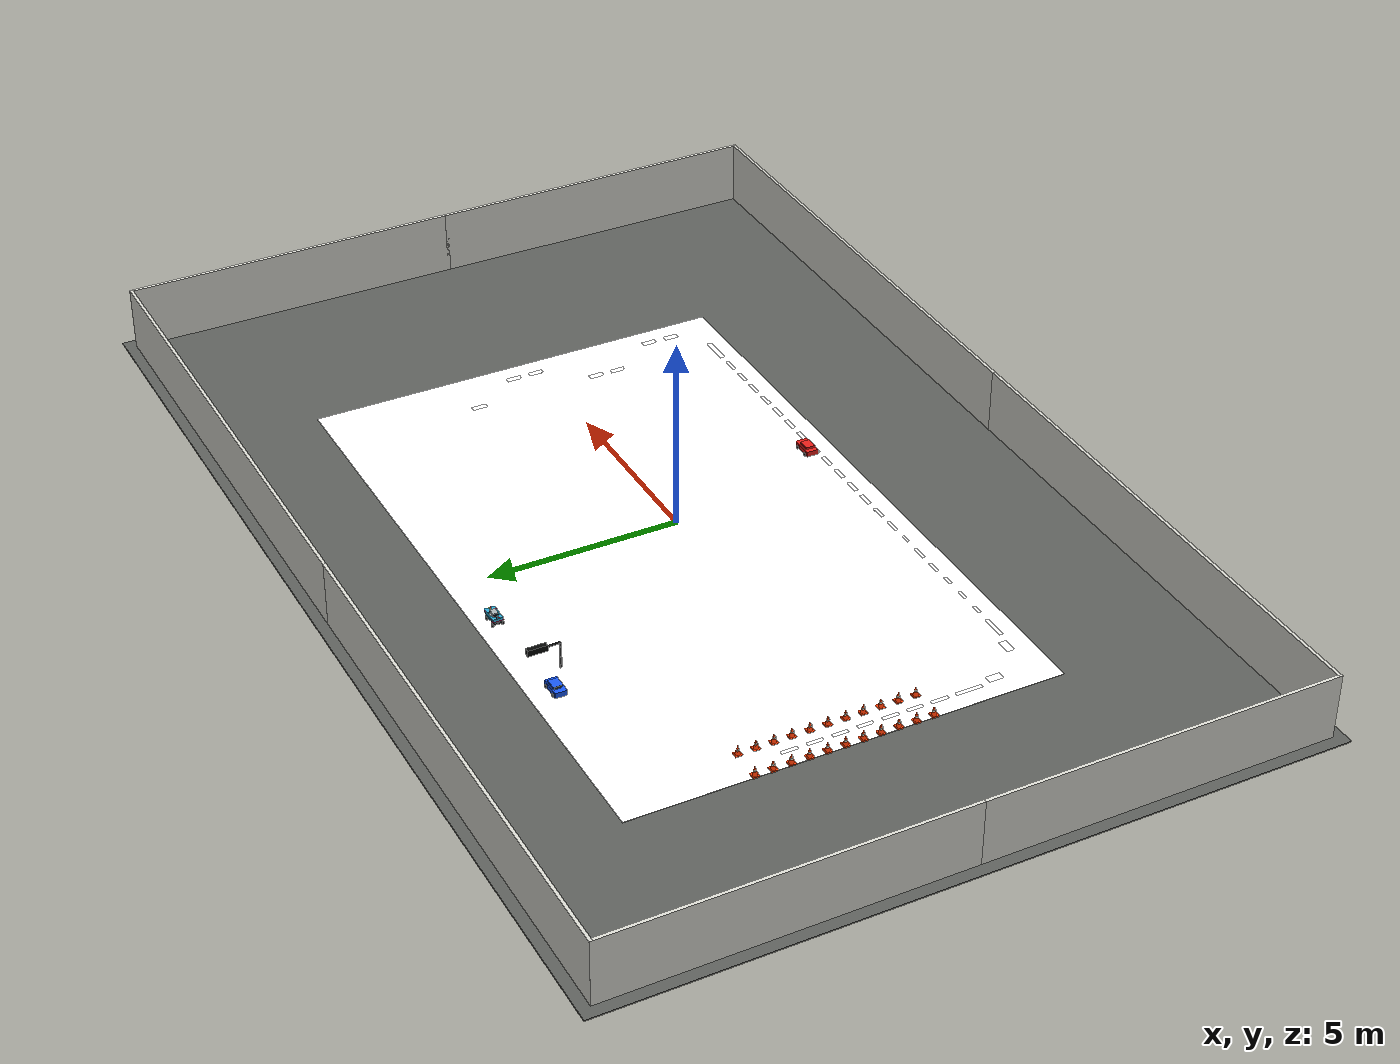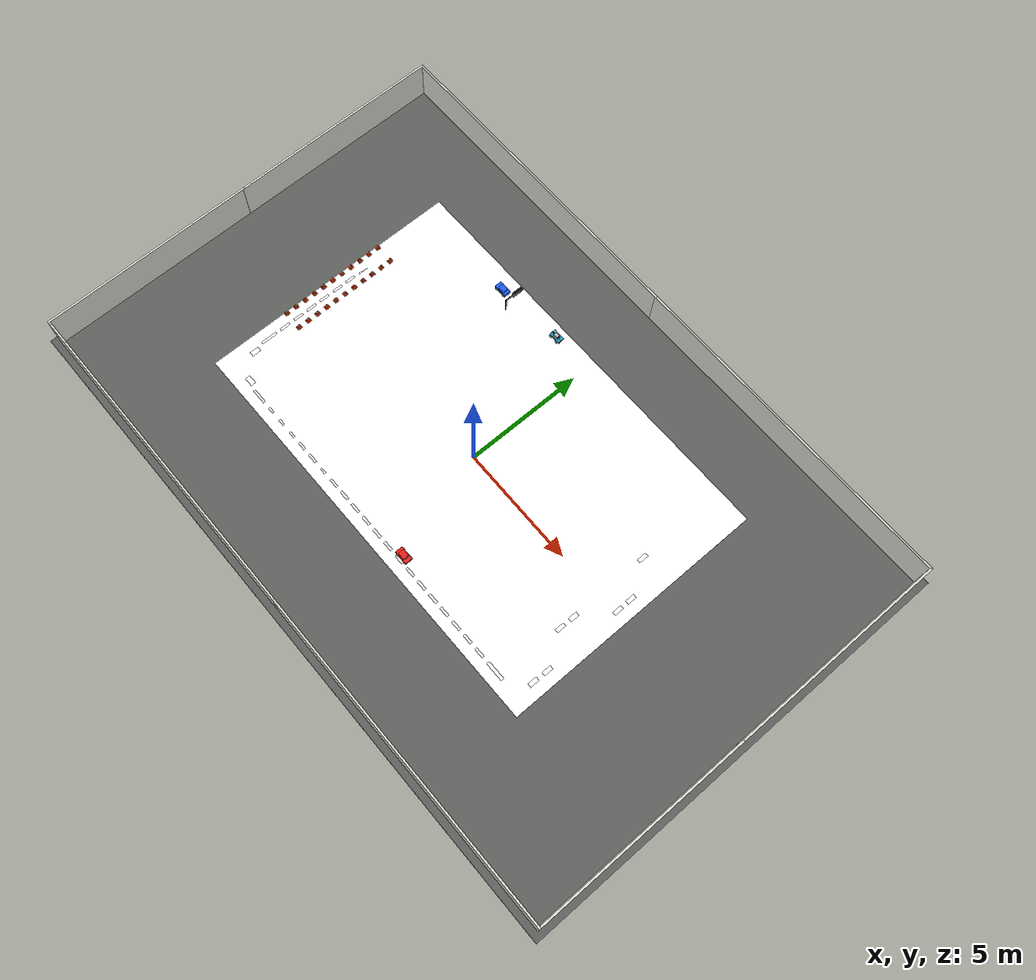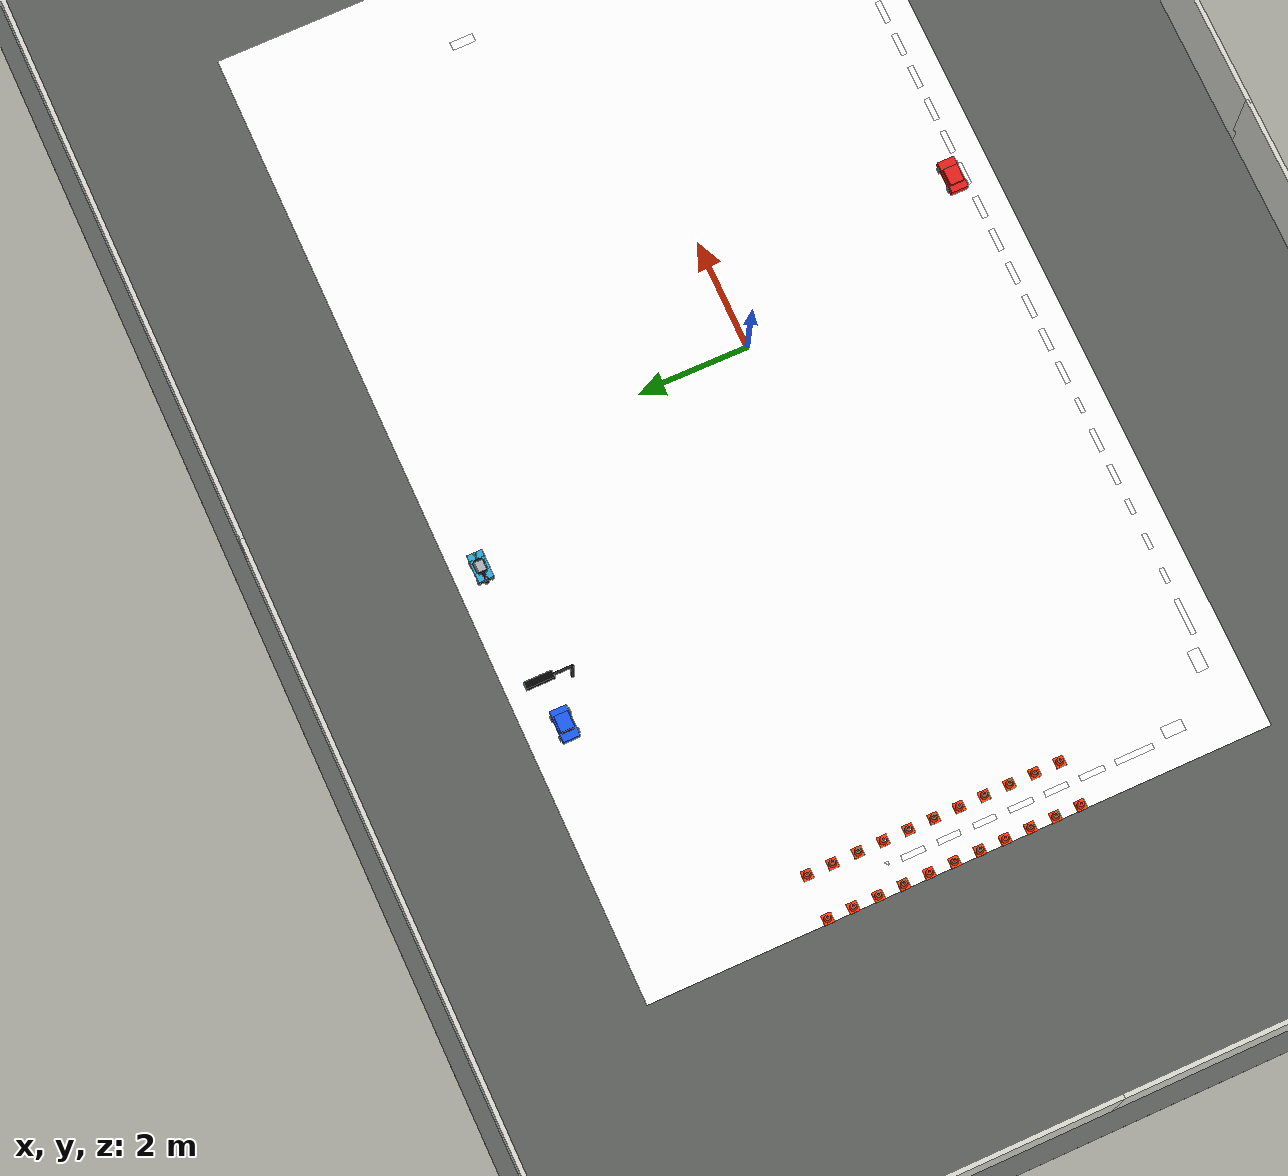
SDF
<?xml version="1.0"?>
<sdf version="1.7">
  <world name="kookmin_xycar_track">
    <gravity>0 0 -9.8</gravity>
    <magnetic_field>6e-6 2.3e-5 -4.2e-5</magnetic_field>
    <atmosphere type="adiabatic"/>
    <physics name="default_physics" default="1" type="ignored"><max_step_size>0.001</max_step_size><real_time_factor>1</real_time_factor><real_time_update_rate>1000</real_time_update_rate></physics>
    <plugin filename="gz-sim-physics-system" name="gz::sim::systems::Physics"/>
    <plugin filename="gz-sim-user-commands-system" name="gz::sim::systems::UserCommands"/>
    <plugin filename="gz-sim-scene-broadcaster-system" name="gz::sim::systems::SceneBroadcaster"/>
    <plugin filename="gz-sim-sensors-system" name="gz::sim::systems::Sensors"><render_engine>ogre2</render_engine></plugin>
    <scene><ambient>0.75 0.75 0.75 1</ambient><background>0.82 0.84 0.86 1</background><shadows>false</shadows></scene>
    <light name="sun" type="directional"><cast_shadows>false</cast_shadows><pose>0 0 10 0 0 0</pose><diffuse>0.82 0.82 0.82 1</diffuse><specular>0.2 0.2 0.2 1</specular><direction>-0.45 0.20 -0.88</direction></light>

    <model name="kookmin_track">
      <static>true</static>
      <link name="floor_base">
        <pose>0 0 -0.015 0 0 0</pose>
        <collision name="collision">
          <geometry><box><size>28.3000 18.6000 0.0300</size></box></geometry>
          <surface><friction><ode><mu>50</mu><mu2>50</mu2></ode><bullet><friction>1</friction><rolling_friction>0.1</rolling_friction></bullet></friction></surface>
        </collision>
        <visual name="visual">
          <geometry><box><size>28.3000 18.6000 0.0300</size></box></geometry>
          <material><ambient>0.3608 0.3686 0.3569 1</ambient><diffuse>0.3608 0.3686 0.3569 1</diffuse></material>
        </visual>
      </link>
      <link name="track_texture_surface">
        <pose>0 0 0.006 0 0 0</pose>
        <visual name="visual">
          <geometry><plane><normal>0 0 1</normal><size>28.3000 18.6000</size></plane></geometry>
          <material><ambient>1 1 1 1</ambient><diffuse>1 1 1 1</diffuse><pbr><metal><albedo_map>file://media/materials/textures/kookmin_cad_v4_road.png</albedo_map><roughness>1</roughness><metalness>0</metalness></metal></pbr></material>
        </visual>
      </link>
    </model>

    <model name="cad_outer_wall">
      <static>true</static>

      <link name="cad_outer_wall_000">
        <pose>-13.8145 -4.4879 0.8500 0.000000 0.000000 -1.570796</pose>
        <collision name="collision">
          <geometry><box><size>9.0559 0.0800 1.7000</size></box></geometry>
          <surface>
            <friction>
              <ode><mu>50</mu><mu2>50</mu2></ode>
              <bullet><friction>1</friction><rolling_friction>0.1</rolling_friction></bullet>
            </friction>
          </surface>
        </collision>
        <visual name="visual">
          <geometry><box><size>9.0559 0.0800 1.7000</size></box></geometry>
          <material><ambient>0.8549 0.8549 0.8235 1</ambient><diffuse>0.8549 0.8549 0.8235 1</diffuse></material>
        </visual>
      </link>
      <link name="cad_outer_wall_001">
        <pose>-6.9072 -8.9759 0.8500 0.000000 0.000000 0.000000</pose>
        <collision name="collision">
          <geometry><box><size>13.8945 0.0800 1.7000</size></box></geometry>
          <surface>
            <friction>
              <ode><mu>50</mu><mu2>50</mu2></ode>
              <bullet><friction>1</friction><rolling_friction>0.1</rolling_friction></bullet>
            </friction>
          </surface>
        </collision>
        <visual name="visual">
          <geometry><box><size>13.8945 0.0800 1.7000</size></box></geometry>
          <material><ambient>0.8549 0.8549 0.8235 1</ambient><diffuse>0.8549 0.8549 0.8235 1</diffuse></material>
        </visual>
      </link>
      <link name="cad_outer_wall_002">
        <pose>6.9072 -8.9759 0.8500 0.000000 0.000000 0.000000</pose>
        <collision name="collision">
          <geometry><box><size>13.8945 0.0800 1.7000</size></box></geometry>
          <surface>
            <friction>
              <ode><mu>50</mu><mu2>50</mu2></ode>
              <bullet><friction>1</friction><rolling_friction>0.1</rolling_friction></bullet>
            </friction>
          </surface>
        </collision>
        <visual name="visual">
          <geometry><box><size>13.8945 0.0800 1.7000</size></box></geometry>
          <material><ambient>0.8549 0.8549 0.8235 1</ambient><diffuse>0.8549 0.8549 0.8235 1</diffuse></material>
        </visual>
      </link>
      <link name="cad_outer_wall_003">
        <pose>13.8145 -4.4879 0.8500 0.000000 0.000000 1.570796</pose>
        <collision name="collision">
          <geometry><box><size>9.0559 0.0800 1.7000</size></box></geometry>
          <surface>
            <friction>
              <ode><mu>50</mu><mu2>50</mu2></ode>
              <bullet><friction>1</friction><rolling_friction>0.1</rolling_friction></bullet>
            </friction>
          </surface>
        </collision>
        <visual name="visual">
          <geometry><box><size>9.0559 0.0800 1.7000</size></box></geometry>
          <material><ambient>0.8549 0.8549 0.8235 1</ambient><diffuse>0.8549 0.8549 0.8235 1</diffuse></material>
        </visual>
      </link>
      <link name="cad_outer_wall_004">
        <pose>13.8145 4.4879 0.8500 0.000000 0.000000 1.570796</pose>
        <collision name="collision">
          <geometry><box><size>9.0559 0.0800 1.7000</size></box></geometry>
          <surface>
            <friction>
              <ode><mu>50</mu><mu2>50</mu2></ode>
              <bullet><friction>1</friction><rolling_friction>0.1</rolling_friction></bullet>
            </friction>
          </surface>
        </collision>
        <visual name="visual">
          <geometry><box><size>9.0559 0.0800 1.7000</size></box></geometry>
          <material><ambient>0.8549 0.8549 0.8235 1</ambient><diffuse>0.8549 0.8549 0.8235 1</diffuse></material>
        </visual>
      </link>
      <link name="cad_outer_wall_005">
        <pose>6.9072 8.9759 0.8500 0.000000 0.000000 3.141593</pose>
        <collision name="collision">
          <geometry><box><size>13.8945 0.0800 1.7000</size></box></geometry>
          <surface>
            <friction>
              <ode><mu>50</mu><mu2>50</mu2></ode>
              <bullet><friction>1</friction><rolling_friction>0.1</rolling_friction></bullet>
            </friction>
          </surface>
        </collision>
        <visual name="visual">
          <geometry><box><size>13.8945 0.0800 1.7000</size></box></geometry>
          <material><ambient>0.8549 0.8549 0.8235 1</ambient><diffuse>0.8549 0.8549 0.8235 1</diffuse></material>
        </visual>
      </link>
      <link name="cad_outer_wall_006">
        <pose>-6.9072 8.9759 0.8500 0.000000 0.000000 3.141593</pose>
        <collision name="collision">
          <geometry><box><size>13.8945 0.0800 1.7000</size></box></geometry>
          <surface>
            <friction>
              <ode><mu>50</mu><mu2>50</mu2></ode>
              <bullet><friction>1</friction><rolling_friction>0.1</rolling_friction></bullet>
            </friction>
          </surface>
        </collision>
        <visual name="visual">
          <geometry><box><size>13.8945 0.0800 1.7000</size></box></geometry>
          <material><ambient>0.8549 0.8549 0.8235 1</ambient><diffuse>0.8549 0.8549 0.8235 1</diffuse></material>
        </visual>
      </link>
      <link name="cad_outer_wall_007">
        <pose>-13.8145 4.4879 0.8500 0.000000 0.000000 -1.570796</pose>
        <collision name="collision">
          <geometry><box><size>9.0559 0.0800 1.7000</size></box></geometry>
          <surface>
            <friction>
              <ode><mu>50</mu><mu2>50</mu2></ode>
              <bullet><friction>1</friction><rolling_friction>0.1</rolling_friction></bullet>
            </friction>
          </surface>
        </collision>
        <visual name="visual">
          <geometry><box><size>9.0559 0.0800 1.7000</size></box></geometry>
          <material><ambient>0.8549 0.8549 0.8235 1</ambient><diffuse>0.8549 0.8549 0.8235 1</diffuse></material>
        </visual>
      </link>
    </model>

    <model name="white_line_cad_v4_001">
      <static>true</static>
      <pose>-0.5200 0.5100 0.0140 0 0 0</pose>
      <link name="white_line_cad_v4_001_surface">
        <visual name="visual">
          <cast_shadows>false</cast_shadows>
          <geometry><plane><normal>0 0 1</normal><size>17.5600 11.1000</size></plane></geometry>
          <material>
            <ambient>1 1 1 1</ambient><diffuse>1 1 1 1</diffuse>
            <emissive>0.9490 0.9490 0.9255 1</emissive>
            <pbr><metal><albedo_map>file://media/materials/textures/kookmin_white_line_cad_v4_001.png</albedo_map><roughness>1</roughness><metalness>0</metalness></metal></pbr>
          </material>
        </visual>
      </link>
    </model>
    <model name="white_line_cad_v4_002">
      <static>true</static>
      <pose>-0.5250 0.5050 0.0142 0 0 0</pose>
      <link name="white_line_cad_v4_002_surface">
        <visual name="visual">
          <cast_shadows>false</cast_shadows>
          <geometry><plane><normal>0 0 1</normal><size>15.8700 9.4300</size></plane></geometry>
          <material>
            <ambient>1 1 1 1</ambient><diffuse>1 1 1 1</diffuse>
            <emissive>0.9490 0.9490 0.9255 1</emissive>
            <pbr><metal><albedo_map>file://media/materials/textures/kookmin_white_line_cad_v4_002.png</albedo_map><roughness>1</roughness><metalness>0</metalness></metal></pbr>
          </material>
        </visual>
      </link>
    </model>

    <model name="yellow_centerline_dash_001">
      <static>true</static>
      <pose>-7.0900 5.5700 0.0180 0 0 0</pose>
      <link name="yellow_centerline_dash_001_surface">
        <visual name="visual">
          <cast_shadows>false</cast_shadows>
          <geometry><plane><normal>0 0 1</normal><size>0.6600 0.1200</size></plane></geometry>
          <material>
            <ambient>1 1 1 1</ambient><diffuse>1 1 1 1</diffuse>
            <emissive>1.0000 0.7686 0.0471 1</emissive>
            <pbr><metal><albedo_map>file://media/materials/textures/kookmin_yellow_centerline_cad_v4_dash_001.png</albedo_map><roughness>1</roughness><metalness>0</metalness></metal></pbr>
          </material>
        </visual>
      </link>
    </model>
    <model name="yellow_centerline_dash_002">
      <static>true</static>
      <pose>-6.3450 5.5800 0.0181 0 0 0</pose>
      <link name="yellow_centerline_dash_002_surface">
        <visual name="visual">
          <cast_shadows>false</cast_shadows>
          <geometry><plane><normal>0 0 1</normal><size>0.4100 0.1000</size></plane></geometry>
          <material>
            <ambient>1 1 1 1</ambient><diffuse>1 1 1 1</diffuse>
            <emissive>1.0000 0.7686 0.0471 1</emissive>
            <pbr><metal><albedo_map>file://media/materials/textures/kookmin_yellow_centerline_cad_v4_dash_002.png</albedo_map><roughness>1</roughness><metalness>0</metalness></metal></pbr>
          </material>
        </visual>
      </link>
    </model>
    <model name="yellow_centerline_dash_003">
      <static>true</static>
      <pose>-5.7200 5.5800 0.0181 0 0 0</pose>
      <link name="yellow_centerline_dash_003_surface">
        <visual name="visual">
          <cast_shadows>false</cast_shadows>
          <geometry><plane><normal>0 0 1</normal><size>0.4000 0.1000</size></plane></geometry>
          <material>
            <ambient>1 1 1 1</ambient><diffuse>1 1 1 1</diffuse>
            <emissive>1.0000 0.7686 0.0471 1</emissive>
            <pbr><metal><albedo_map>file://media/materials/textures/kookmin_yellow_centerline_cad_v4_dash_003.png</albedo_map><roughness>1</roughness><metalness>0</metalness></metal></pbr>
          </material>
        </visual>
      </link>
    </model>
    <model name="yellow_centerline_dash_004">
      <static>true</static>
      <pose>-5.0750 5.5800 0.0181 0 0 0</pose>
      <link name="yellow_centerline_dash_004_surface">
        <visual name="visual">
          <cast_shadows>false</cast_shadows>
          <geometry><plane><normal>0 0 1</normal><size>0.3900 0.1000</size></plane></geometry>
          <material>
            <ambient>1 1 1 1</ambient><diffuse>1 1 1 1</diffuse>
            <emissive>1.0000 0.7686 0.0471 1</emissive>
            <pbr><metal><albedo_map>file://media/materials/textures/kookmin_yellow_centerline_cad_v4_dash_004.png</albedo_map><roughness>1</roughness><metalness>0</metalness></metal></pbr>
          </material>
        </visual>
      </link>
    </model>
    <model name="yellow_centerline_dash_005">
      <static>true</static>
      <pose>-4.4450 5.5800 0.0182 0 0 0</pose>
      <link name="yellow_centerline_dash_005_surface">
        <visual name="visual">
          <cast_shadows>false</cast_shadows>
          <geometry><plane><normal>0 0 1</normal><size>0.4100 0.1000</size></plane></geometry>
          <material>
            <ambient>1 1 1 1</ambient><diffuse>1 1 1 1</diffuse>
            <emissive>1.0000 0.7686 0.0471 1</emissive>
            <pbr><metal><albedo_map>file://media/materials/textures/kookmin_yellow_centerline_cad_v4_dash_005.png</albedo_map><roughness>1</roughness><metalness>0</metalness></metal></pbr>
          </material>
        </visual>
      </link>
    </model>
    <model name="yellow_centerline_dash_006">
      <static>true</static>
      <pose>-3.8050 5.5800 0.0182 0 0 0</pose>
      <link name="yellow_centerline_dash_006_surface">
        <visual name="visual">
          <cast_shadows>false</cast_shadows>
          <geometry><plane><normal>0 0 1</normal><size>0.4100 0.1000</size></plane></geometry>
          <material>
            <ambient>1 1 1 1</ambient><diffuse>1 1 1 1</diffuse>
            <emissive>1.0000 0.7686 0.0471 1</emissive>
            <pbr><metal><albedo_map>file://media/materials/textures/kookmin_yellow_centerline_cad_v4_dash_006.png</albedo_map><roughness>1</roughness><metalness>0</metalness></metal></pbr>
          </material>
        </visual>
      </link>
    </model>
    <model name="yellow_centerline_dash_007">
      <static>true</static>
      <pose>-3.1800 5.5800 0.0183 0 0 0</pose>
      <link name="yellow_centerline_dash_007_surface">
        <visual name="visual">
          <cast_shadows>false</cast_shadows>
          <geometry><plane><normal>0 0 1</normal><size>0.4000 0.1000</size></plane></geometry>
          <material>
            <ambient>1 1 1 1</ambient><diffuse>1 1 1 1</diffuse>
            <emissive>1.0000 0.7686 0.0471 1</emissive>
            <pbr><metal><albedo_map>file://media/materials/textures/kookmin_yellow_centerline_cad_v4_dash_007.png</albedo_map><roughness>1</roughness><metalness>0</metalness></metal></pbr>
          </material>
        </visual>
      </link>
    </model>
    <model name="yellow_centerline_dash_008">
      <static>true</static>
      <pose>-2.5400 5.5800 0.0183 0 0 0</pose>
      <link name="yellow_centerline_dash_008_surface">
        <visual name="visual">
          <cast_shadows>false</cast_shadows>
          <geometry><plane><normal>0 0 1</normal><size>0.4000 0.1000</size></plane></geometry>
          <material>
            <ambient>1 1 1 1</ambient><diffuse>1 1 1 1</diffuse>
            <emissive>1.0000 0.7686 0.0471 1</emissive>
            <pbr><metal><albedo_map>file://media/materials/textures/kookmin_yellow_centerline_cad_v4_dash_008.png</albedo_map><roughness>1</roughness><metalness>0</metalness></metal></pbr>
          </material>
        </visual>
      </link>
    </model>
    <model name="yellow_centerline_dash_009">
      <static>true</static>
      <pose>-1.9150 5.5800 0.0184 0 0 0</pose>
      <link name="yellow_centerline_dash_009_surface">
        <visual name="visual">
          <cast_shadows>false</cast_shadows>
          <geometry><plane><normal>0 0 1</normal><size>0.3900 0.1000</size></plane></geometry>
          <material>
            <ambient>1 1 1 1</ambient><diffuse>1 1 1 1</diffuse>
            <emissive>1.0000 0.7686 0.0471 1</emissive>
            <pbr><metal><albedo_map>file://media/materials/textures/kookmin_yellow_centerline_cad_v4_dash_009.png</albedo_map><roughness>1</roughness><metalness>0</metalness></metal></pbr>
          </material>
        </visual>
      </link>
    </model>
    <model name="yellow_centerline_dash_010">
      <static>true</static>
      <pose>-1.2750 5.5800 0.0184 0 0 0</pose>
      <link name="yellow_centerline_dash_010_surface">
        <visual name="visual">
          <cast_shadows>false</cast_shadows>
          <geometry><plane><normal>0 0 1</normal><size>0.3900 0.1000</size></plane></geometry>
          <material>
            <ambient>1 1 1 1</ambient><diffuse>1 1 1 1</diffuse>
            <emissive>1.0000 0.7686 0.0471 1</emissive>
            <pbr><metal><albedo_map>file://media/materials/textures/kookmin_yellow_centerline_cad_v4_dash_010.png</albedo_map><roughness>1</roughness><metalness>0</metalness></metal></pbr>
          </material>
        </visual>
      </link>
    </model>
    <model name="yellow_centerline_dash_011">
      <static>true</static>
      <pose>-0.6450 5.5800 0.0185 0 0 0</pose>
      <link name="yellow_centerline_dash_011_surface">
        <visual name="visual">
          <cast_shadows>false</cast_shadows>
          <geometry><plane><normal>0 0 1</normal><size>0.4100 0.1000</size></plane></geometry>
          <material>
            <ambient>1 1 1 1</ambient><diffuse>1 1 1 1</diffuse>
            <emissive>1.0000 0.7686 0.0471 1</emissive>
            <pbr><metal><albedo_map>file://media/materials/textures/kookmin_yellow_centerline_cad_v4_dash_011.png</albedo_map><roughness>1</roughness><metalness>0</metalness></metal></pbr>
          </material>
        </visual>
      </link>
    </model>
    <model name="yellow_centerline_dash_012">
      <static>true</static>
      <pose>-0.0050 5.5800 0.0185 0 0 0</pose>
      <link name="yellow_centerline_dash_012_surface">
        <visual name="visual">
          <cast_shadows>false</cast_shadows>
          <geometry><plane><normal>0 0 1</normal><size>0.4100 0.1000</size></plane></geometry>
          <material>
            <ambient>1 1 1 1</ambient><diffuse>1 1 1 1</diffuse>
            <emissive>1.0000 0.7686 0.0471 1</emissive>
            <pbr><metal><albedo_map>file://media/materials/textures/kookmin_yellow_centerline_cad_v4_dash_012.png</albedo_map><roughness>1</roughness><metalness>0</metalness></metal></pbr>
          </material>
        </visual>
      </link>
    </model>
    <model name="yellow_centerline_dash_013">
      <static>true</static>
      <pose>0.6350 5.5800 0.0186 0 0 0</pose>
      <link name="yellow_centerline_dash_013_surface">
        <visual name="visual">
          <cast_shadows>false</cast_shadows>
          <geometry><plane><normal>0 0 1</normal><size>0.4100 0.1000</size></plane></geometry>
          <material>
            <ambient>1 1 1 1</ambient><diffuse>1 1 1 1</diffuse>
            <emissive>1.0000 0.7686 0.0471 1</emissive>
            <pbr><metal><albedo_map>file://media/materials/textures/kookmin_yellow_centerline_cad_v4_dash_013.png</albedo_map><roughness>1</roughness><metalness>0</metalness></metal></pbr>
          </material>
        </visual>
      </link>
    </model>
    <model name="yellow_centerline_dash_014">
      <static>true</static>
      <pose>1.2750 5.5800 0.0186 0 0 0</pose>
      <link name="yellow_centerline_dash_014_surface">
        <visual name="visual">
          <cast_shadows>false</cast_shadows>
          <geometry><plane><normal>0 0 1</normal><size>0.4100 0.1000</size></plane></geometry>
          <material>
            <ambient>1 1 1 1</ambient><diffuse>1 1 1 1</diffuse>
            <emissive>1.0000 0.7686 0.0471 1</emissive>
            <pbr><metal><albedo_map>file://media/materials/textures/kookmin_yellow_centerline_cad_v4_dash_014.png</albedo_map><roughness>1</roughness><metalness>0</metalness></metal></pbr>
          </material>
        </visual>
      </link>
    </model>
    <model name="yellow_centerline_dash_015">
      <static>true</static>
      <pose>1.8950 5.5800 0.0187 0 0 0</pose>
      <link name="yellow_centerline_dash_015_surface">
        <visual name="visual">
          <cast_shadows>false</cast_shadows>
          <geometry><plane><normal>0 0 1</normal><size>0.4100 0.1000</size></plane></geometry>
          <material>
            <ambient>1 1 1 1</ambient><diffuse>1 1 1 1</diffuse>
            <emissive>1.0000 0.7686 0.0471 1</emissive>
            <pbr><metal><albedo_map>file://media/materials/textures/kookmin_yellow_centerline_cad_v4_dash_015.png</albedo_map><roughness>1</roughness><metalness>0</metalness></metal></pbr>
          </material>
        </visual>
      </link>
    </model>
    <model name="yellow_centerline_dash_016">
      <static>true</static>
      <pose>2.5350 5.5800 0.0187 0 0 0</pose>
      <link name="yellow_centerline_dash_016_surface">
        <visual name="visual">
          <cast_shadows>false</cast_shadows>
          <geometry><plane><normal>0 0 1</normal><size>0.4100 0.1000</size></plane></geometry>
          <material>
            <ambient>1 1 1 1</ambient><diffuse>1 1 1 1</diffuse>
            <emissive>1.0000 0.7686 0.0471 1</emissive>
            <pbr><metal><albedo_map>file://media/materials/textures/kookmin_yellow_centerline_cad_v4_dash_016.png</albedo_map><roughness>1</roughness><metalness>0</metalness></metal></pbr>
          </material>
        </visual>
      </link>
    </model>
    <model name="yellow_centerline_dash_017">
      <static>true</static>
      <pose>3.1750 5.5800 0.0188 0 0 0</pose>
      <link name="yellow_centerline_dash_017_surface">
        <visual name="visual">
          <cast_shadows>false</cast_shadows>
          <geometry><plane><normal>0 0 1</normal><size>0.4100 0.1000</size></plane></geometry>
          <material>
            <ambient>1 1 1 1</ambient><diffuse>1 1 1 1</diffuse>
            <emissive>1.0000 0.7686 0.0471 1</emissive>
            <pbr><metal><albedo_map>file://media/materials/textures/kookmin_yellow_centerline_cad_v4_dash_017.png</albedo_map><roughness>1</roughness><metalness>0</metalness></metal></pbr>
          </material>
        </visual>
      </link>
    </model>
    <model name="yellow_centerline_dash_018">
      <static>true</static>
      <pose>3.8150 5.5800 0.0188 0 0 0</pose>
      <link name="yellow_centerline_dash_018_surface">
        <visual name="visual">
          <cast_shadows>false</cast_shadows>
          <geometry><plane><normal>0 0 1</normal><size>0.4100 0.1000</size></plane></geometry>
          <material>
            <ambient>1 1 1 1</ambient><diffuse>1 1 1 1</diffuse>
            <emissive>1.0000 0.7686 0.0471 1</emissive>
            <pbr><metal><albedo_map>file://media/materials/textures/kookmin_yellow_centerline_cad_v4_dash_018.png</albedo_map><roughness>1</roughness><metalness>0</metalness></metal></pbr>
          </material>
        </visual>
      </link>
    </model>
    <model name="yellow_centerline_dash_019">
      <static>true</static>
      <pose>4.4450 5.5800 0.0189 0 0 0</pose>
      <link name="yellow_centerline_dash_019_surface">
        <visual name="visual">
          <cast_shadows>false</cast_shadows>
          <geometry><plane><normal>0 0 1</normal><size>0.3900 0.1000</size></plane></geometry>
          <material>
            <ambient>1 1 1 1</ambient><diffuse>1 1 1 1</diffuse>
            <emissive>1.0000 0.7686 0.0471 1</emissive>
            <pbr><metal><albedo_map>file://media/materials/textures/kookmin_yellow_centerline_cad_v4_dash_019.png</albedo_map><roughness>1</roughness><metalness>0</metalness></metal></pbr>
          </material>
        </visual>
      </link>
    </model>
    <model name="yellow_centerline_dash_020">
      <static>true</static>
      <pose>5.0850 5.5800 0.0189 0 0 0</pose>
      <link name="yellow_centerline_dash_020_surface">
        <visual name="visual">
          <cast_shadows>false</cast_shadows>
          <geometry><plane><normal>0 0 1</normal><size>0.4300 0.1000</size></plane></geometry>
          <material>
            <ambient>1 1 1 1</ambient><diffuse>1 1 1 1</diffuse>
            <emissive>1.0000 0.7686 0.0471 1</emissive>
            <pbr><metal><albedo_map>file://media/materials/textures/kookmin_yellow_centerline_cad_v4_dash_020.png</albedo_map><roughness>1</roughness><metalness>0</metalness></metal></pbr>
          </material>
        </visual>
      </link>
    </model>
    <model name="yellow_centerline_dash_021">
      <static>true</static>
      <pose>5.7350 5.5800 0.0190 0 0 0</pose>
      <link name="yellow_centerline_dash_021_surface">
        <visual name="visual">
          <cast_shadows>false</cast_shadows>
          <geometry><plane><normal>0 0 1</normal><size>0.4100 0.1000</size></plane></geometry>
          <material>
            <ambient>1 1 1 1</ambient><diffuse>1 1 1 1</diffuse>
            <emissive>1.0000 0.7686 0.0471 1</emissive>
            <pbr><metal><albedo_map>file://media/materials/textures/kookmin_yellow_centerline_cad_v4_dash_021.png</albedo_map><roughness>1</roughness><metalness>0</metalness></metal></pbr>
          </material>
        </visual>
      </link>
    </model>
    <model name="yellow_centerline_dash_022">
      <static>true</static>
      <pose>6.5650 5.5600 0.0190 0 0 0</pose>
      <link name="yellow_centerline_dash_022_surface">
        <visual name="visual">
          <cast_shadows>false</cast_shadows>
          <geometry><plane><normal>0 0 1</normal><size>0.7900 0.1400</size></plane></geometry>
          <material>
            <ambient>1 1 1 1</ambient><diffuse>1 1 1 1</diffuse>
            <emissive>1.0000 0.7686 0.0471 1</emissive>
            <pbr><metal><albedo_map>file://media/materials/textures/kookmin_yellow_centerline_cad_v4_dash_022.png</albedo_map><roughness>1</roughness><metalness>0</metalness></metal></pbr>
          </material>
        </visual>
      </link>
    </model>
    <model name="yellow_centerline_dash_023">
      <static>true</static>
      <pose>-7.8200 5.4350 0.0191 0 0 0</pose>
      <link name="yellow_centerline_dash_023_surface">
        <visual name="visual">
          <cast_shadows>false</cast_shadows>
          <geometry><plane><normal>0 0 1</normal><size>0.3800 0.2100</size></plane></geometry>
          <material>
            <ambient>1 1 1 1</ambient><diffuse>1 1 1 1</diffuse>
            <emissive>1.0000 0.7686 0.0471 1</emissive>
            <pbr><metal><albedo_map>file://media/materials/textures/kookmin_yellow_centerline_cad_v4_dash_023.png</albedo_map><roughness>1</roughness><metalness>0</metalness></metal></pbr>
          </material>
        </visual>
      </link>
    </model>
    <model name="yellow_centerline_dash_024">
      <static>true</static>
      <pose>7.7250 4.7650 0.0192 0 0 0</pose>
      <link name="yellow_centerline_dash_024_surface">
        <visual name="visual">
          <cast_shadows>false</cast_shadows>
          <geometry><plane><normal>0 0 1</normal><size>0.1700 0.3500</size></plane></geometry>
          <material>
            <ambient>1 1 1 1</ambient><diffuse>1 1 1 1</diffuse>
            <emissive>1.0000 0.7686 0.0471 1</emissive>
            <pbr><metal><albedo_map>file://media/materials/textures/kookmin_yellow_centerline_cad_v4_dash_024.png</albedo_map><roughness>1</roughness><metalness>0</metalness></metal></pbr>
          </material>
        </visual>
      </link>
    </model>
    <model name="yellow_centerline_dash_025">
      <static>true</static>
      <pose>-8.6900 4.5500 0.0192 0 0 0</pose>
      <link name="yellow_centerline_dash_025_surface">
        <visual name="visual">
          <cast_shadows>false</cast_shadows>
          <geometry><plane><normal>0 0 1</normal><size>0.2000 0.3800</size></plane></geometry>
          <material>
            <ambient>1 1 1 1</ambient><diffuse>1 1 1 1</diffuse>
            <emissive>1.0000 0.7686 0.0471 1</emissive>
            <pbr><metal><albedo_map>file://media/materials/textures/kookmin_yellow_centerline_cad_v4_dash_025.png</albedo_map><roughness>1</roughness><metalness>0</metalness></metal></pbr>
          </material>
        </visual>
      </link>
    </model>
    <model name="yellow_centerline_dash_026">
      <static>true</static>
      <pose>7.7600 4.1400 0.0192 0 0 0</pose>
      <link name="yellow_centerline_dash_026_surface">
        <visual name="visual">
          <cast_shadows>false</cast_shadows>
          <geometry><plane><normal>0 0 1</normal><size>0.1400 0.3800</size></plane></geometry>
          <material>
            <ambient>1 1 1 1</ambient><diffuse>1 1 1 1</diffuse>
            <emissive>1.0000 0.7686 0.0471 1</emissive>
            <pbr><metal><albedo_map>file://media/materials/textures/kookmin_yellow_centerline_cad_v4_dash_026.png</albedo_map><roughness>1</roughness><metalness>0</metalness></metal></pbr>
          </material>
        </visual>
      </link>
    </model>
    <model name="yellow_centerline_dash_027">
      <static>true</static>
      <pose>-8.8200 3.8000 0.0193 0 0 0</pose>
      <link name="yellow_centerline_dash_027_surface">
        <visual name="visual">
          <cast_shadows>false</cast_shadows>
          <geometry><plane><normal>0 0 1</normal><size>0.1000 0.6400</size></plane></geometry>
          <material>
            <ambient>1 1 1 1</ambient><diffuse>1 1 1 1</diffuse>
            <emissive>1.0000 0.7686 0.0471 1</emissive>
            <pbr><metal><albedo_map>file://media/materials/textures/kookmin_yellow_centerline_cad_v4_dash_027.png</albedo_map><roughness>1</roughness><metalness>0</metalness></metal></pbr>
          </material>
        </visual>
      </link>
    </model>
    <model name="yellow_centerline_dash_028">
      <static>true</static>
      <pose>-8.8200 3.0500 0.0193 0 0 0</pose>
      <link name="yellow_centerline_dash_028_surface">
        <visual name="visual">
          <cast_shadows>false</cast_shadows>
          <geometry><plane><normal>0 0 1</normal><size>0.1000 0.4400</size></plane></geometry>
          <material>
            <ambient>1 1 1 1</ambient><diffuse>1 1 1 1</diffuse>
            <emissive>1.0000 0.7686 0.0471 1</emissive>
            <pbr><metal><albedo_map>file://media/materials/textures/kookmin_yellow_centerline_cad_v4_dash_028.png</albedo_map><roughness>1</roughness><metalness>0</metalness></metal></pbr>
          </material>
        </visual>
      </link>
    </model>
    <model name="yellow_centerline_dash_029">
      <static>true</static>
      <pose>6.9000 2.7750 0.0194 0 0 0</pose>
      <link name="yellow_centerline_dash_029_surface">
        <visual name="visual">
          <cast_shadows>false</cast_shadows>
          <geometry><plane><normal>0 0 1</normal><size>0.1800 0.3900</size></plane></geometry>
          <material>
            <ambient>1 1 1 1</ambient><diffuse>1 1 1 1</diffuse>
            <emissive>1.0000 0.7686 0.0471 1</emissive>
            <pbr><metal><albedo_map>file://media/materials/textures/kookmin_yellow_centerline_cad_v4_dash_029.png</albedo_map><roughness>1</roughness><metalness>0</metalness></metal></pbr>
          </material>
        </visual>
      </link>
    </model>
    <model name="yellow_centerline_dash_030">
      <static>true</static>
      <pose>-8.8200 2.4200 0.0194 0 0 0</pose>
      <link name="yellow_centerline_dash_030_surface">
        <visual name="visual">
          <cast_shadows>false</cast_shadows>
          <geometry><plane><normal>0 0 1</normal><size>0.1000 0.4200</size></plane></geometry>
          <material>
            <ambient>1 1 1 1</ambient><diffuse>1 1 1 1</diffuse>
            <emissive>1.0000 0.7686 0.0471 1</emissive>
            <pbr><metal><albedo_map>file://media/materials/textures/kookmin_yellow_centerline_cad_v4_dash_030.png</albedo_map><roughness>1</roughness><metalness>0</metalness></metal></pbr>
          </material>
        </visual>
      </link>
    </model>
    <model name="yellow_centerline_dash_031">
      <static>true</static>
      <pose>6.8850 2.1450 0.0195 0 0 0</pose>
      <link name="yellow_centerline_dash_031_surface">
        <visual name="visual">
          <cast_shadows>false</cast_shadows>
          <geometry><plane><normal>0 0 1</normal><size>0.1500 0.4100</size></plane></geometry>
          <material>
            <ambient>1 1 1 1</ambient><diffuse>1 1 1 1</diffuse>
            <emissive>1.0000 0.7686 0.0471 1</emissive>
            <pbr><metal><albedo_map>file://media/materials/textures/kookmin_yellow_centerline_cad_v4_dash_031.png</albedo_map><roughness>1</roughness><metalness>0</metalness></metal></pbr>
          </material>
        </visual>
      </link>
    </model>
    <model name="yellow_centerline_dash_032">
      <static>true</static>
      <pose>-8.8200 1.7800 0.0195 0 0 0</pose>
      <link name="yellow_centerline_dash_032_surface">
        <visual name="visual">
          <cast_shadows>false</cast_shadows>
          <geometry><plane><normal>0 0 1</normal><size>0.1000 0.4200</size></plane></geometry>
          <material>
            <ambient>1 1 1 1</ambient><diffuse>1 1 1 1</diffuse>
            <emissive>1.0000 0.7686 0.0471 1</emissive>
            <pbr><metal><albedo_map>file://media/materials/textures/kookmin_yellow_centerline_cad_v4_dash_032.png</albedo_map><roughness>1</roughness><metalness>0</metalness></metal></pbr>
          </material>
        </visual>
      </link>
    </model>
    <model name="yellow_centerline_dash_033">
      <static>true</static>
      <pose>-8.8200 1.1450 0.0196 0 0 0</pose>
      <link name="yellow_centerline_dash_033_surface">
        <visual name="visual">
          <cast_shadows>false</cast_shadows>
          <geometry><plane><normal>0 0 1</normal><size>0.1000 0.4100</size></plane></geometry>
          <material>
            <ambient>1 1 1 1</ambient><diffuse>1 1 1 1</diffuse>
            <emissive>1.0000 0.7686 0.0471 1</emissive>
            <pbr><metal><albedo_map>file://media/materials/textures/kookmin_yellow_centerline_cad_v4_dash_033.png</albedo_map><roughness>1</roughness><metalness>0</metalness></metal></pbr>
          </material>
        </visual>
      </link>
    </model>
    <model name="yellow_centerline_dash_034">
      <static>true</static>
      <pose>7.7300 0.7850 0.0196 0 0 0</pose>
      <link name="yellow_centerline_dash_034_surface">
        <visual name="visual">
          <cast_shadows>false</cast_shadows>
          <geometry><plane><normal>0 0 1</normal><size>0.1600 0.3900</size></plane></geometry>
          <material>
            <ambient>1 1 1 1</ambient><diffuse>1 1 1 1</diffuse>
            <emissive>1.0000 0.7686 0.0471 1</emissive>
            <pbr><metal><albedo_map>file://media/materials/textures/kookmin_yellow_centerline_cad_v4_dash_034.png</albedo_map><roughness>1</roughness><metalness>0</metalness></metal></pbr>
          </material>
        </visual>
      </link>
    </model>
    <model name="yellow_centerline_dash_035">
      <static>true</static>
      <pose>-8.8200 0.5100 0.0197 0 0 0</pose>
      <link name="yellow_centerline_dash_035_surface">
        <visual name="visual">
          <cast_shadows>false</cast_shadows>
          <geometry><plane><normal>0 0 1</normal><size>0.1000 0.4000</size></plane></geometry>
          <material>
            <ambient>1 1 1 1</ambient><diffuse>1 1 1 1</diffuse>
            <emissive>1.0000 0.7686 0.0471 1</emissive>
            <pbr><metal><albedo_map>file://media/materials/textures/kookmin_yellow_centerline_cad_v4_dash_035.png</albedo_map><roughness>1</roughness><metalness>0</metalness></metal></pbr>
          </material>
        </visual>
      </link>
    </model>
    <model name="yellow_centerline_dash_036">
      <static>true</static>
      <pose>7.7350 0.1650 0.0198 0 0 0</pose>
      <link name="yellow_centerline_dash_036_surface">
        <visual name="visual">
          <cast_shadows>false</cast_shadows>
          <geometry><plane><normal>0 0 1</normal><size>0.1500 0.3900</size></plane></geometry>
          <material>
            <ambient>1 1 1 1</ambient><diffuse>1 1 1 1</diffuse>
            <emissive>1.0000 0.7686 0.0471 1</emissive>
            <pbr><metal><albedo_map>file://media/materials/textures/kookmin_yellow_centerline_cad_v4_dash_036.png</albedo_map><roughness>1</roughness><metalness>0</metalness></metal></pbr>
          </material>
        </visual>
      </link>
    </model>
    <model name="yellow_centerline_dash_037">
      <static>true</static>
      <pose>-8.8200 -0.1300 0.0198 0 0 0</pose>
      <link name="yellow_centerline_dash_037_surface">
        <visual name="visual">
          <cast_shadows>false</cast_shadows>
          <geometry><plane><normal>0 0 1</normal><size>0.1000 0.4000</size></plane></geometry>
          <material>
            <ambient>1 1 1 1</ambient><diffuse>1 1 1 1</diffuse>
            <emissive>1.0000 0.7686 0.0471 1</emissive>
            <pbr><metal><albedo_map>file://media/materials/textures/kookmin_yellow_centerline_cad_v4_dash_037.png</albedo_map><roughness>1</roughness><metalness>0</metalness></metal></pbr>
          </material>
        </visual>
      </link>
    </model>
    <model name="yellow_centerline_dash_038">
      <static>true</static>
      <pose>-8.8200 -0.7750 0.0198 0 0 0</pose>
      <link name="yellow_centerline_dash_038_surface">
        <visual name="visual">
          <cast_shadows>false</cast_shadows>
          <geometry><plane><normal>0 0 1</normal><size>0.1000 0.4300</size></plane></geometry>
          <material>
            <ambient>1 1 1 1</ambient><diffuse>1 1 1 1</diffuse>
            <emissive>1.0000 0.7686 0.0471 1</emissive>
            <pbr><metal><albedo_map>file://media/materials/textures/kookmin_yellow_centerline_cad_v4_dash_038.png</albedo_map><roughness>1</roughness><metalness>0</metalness></metal></pbr>
          </material>
        </visual>
      </link>
    </model>
    <model name="yellow_centerline_dash_039">
      <static>true</static>
      <pose>6.8950 -1.1900 0.0199 0 0 0</pose>
      <link name="yellow_centerline_dash_039_surface">
        <visual name="visual">
          <cast_shadows>false</cast_shadows>
          <geometry><plane><normal>0 0 1</normal><size>0.1700 0.3800</size></plane></geometry>
          <material>
            <ambient>1 1 1 1</ambient><diffuse>1 1 1 1</diffuse>
            <emissive>1.0000 0.7686 0.0471 1</emissive>
            <pbr><metal><albedo_map>file://media/materials/textures/kookmin_yellow_centerline_cad_v4_dash_039.png</albedo_map><roughness>1</roughness><metalness>0</metalness></metal></pbr>
          </material>
        </visual>
      </link>
    </model>
    <model name="yellow_centerline_dash_040">
      <static>true</static>
      <pose>-8.8200 -1.4050 0.0199 0 0 0</pose>
      <link name="yellow_centerline_dash_040_surface">
        <visual name="visual">
          <cast_shadows>false</cast_shadows>
          <geometry><plane><normal>0 0 1</normal><size>0.1000 0.4100</size></plane></geometry>
          <material>
            <ambient>1 1 1 1</ambient><diffuse>1 1 1 1</diffuse>
            <emissive>1.0000 0.7686 0.0471 1</emissive>
            <pbr><metal><albedo_map>file://media/materials/textures/kookmin_yellow_centerline_cad_v4_dash_040.png</albedo_map><roughness>1</roughness><metalness>0</metalness></metal></pbr>
          </material>
        </visual>
      </link>
    </model>
    <model name="yellow_centerline_dash_041">
      <static>true</static>
      <pose>6.8850 -1.8050 0.0200 0 0 0</pose>
      <link name="yellow_centerline_dash_041_surface">
        <visual name="visual">
          <cast_shadows>false</cast_shadows>
          <geometry><plane><normal>0 0 1</normal><size>0.1500 0.3900</size></plane></geometry>
          <material>
            <ambient>1 1 1 1</ambient><diffuse>1 1 1 1</diffuse>
            <emissive>1.0000 0.7686 0.0471 1</emissive>
            <pbr><metal><albedo_map>file://media/materials/textures/kookmin_yellow_centerline_cad_v4_dash_041.png</albedo_map><roughness>1</roughness><metalness>0</metalness></metal></pbr>
          </material>
        </visual>
      </link>
    </model>
    <model name="yellow_centerline_dash_042">
      <static>true</static>
      <pose>-8.8200 -2.0500 0.0200 0 0 0</pose>
      <link name="yellow_centerline_dash_042_surface">
        <visual name="visual">
          <cast_shadows>false</cast_shadows>
          <geometry><plane><normal>0 0 1</normal><size>0.1000 0.4400</size></plane></geometry>
          <material>
            <ambient>1 1 1 1</ambient><diffuse>1 1 1 1</diffuse>
            <emissive>1.0000 0.7686 0.0471 1</emissive>
            <pbr><metal><albedo_map>file://media/materials/textures/kookmin_yellow_centerline_cad_v4_dash_042.png</albedo_map><roughness>1</roughness><metalness>0</metalness></metal></pbr>
          </material>
        </visual>
      </link>
    </model>
    <model name="yellow_centerline_dash_043">
      <static>true</static>
      <pose>-8.8200 -2.8100 0.0201 0 0 0</pose>
      <link name="yellow_centerline_dash_043_surface">
        <visual name="visual">
          <cast_shadows>false</cast_shadows>
          <geometry><plane><normal>0 0 1</normal><size>0.1000 0.6800</size></plane></geometry>
          <material>
            <ambient>1 1 1 1</ambient><diffuse>1 1 1 1</diffuse>
            <emissive>1.0000 0.7686 0.0471 1</emissive>
            <pbr><metal><albedo_map>file://media/materials/textures/kookmin_yellow_centerline_cad_v4_dash_043.png</albedo_map><roughness>1</roughness><metalness>0</metalness></metal></pbr>
          </material>
        </visual>
      </link>
    </model>
    <model name="yellow_centerline_dash_044">
      <static>true</static>
      <pose>7.7300 -3.1600 0.0201 0 0 0</pose>
      <link name="yellow_centerline_dash_044_surface">
        <visual name="visual">
          <cast_shadows>false</cast_shadows>
          <geometry><plane><normal>0 0 1</normal><size>0.1600 0.3800</size></plane></geometry>
          <material>
            <ambient>1 1 1 1</ambient><diffuse>1 1 1 1</diffuse>
            <emissive>1.0000 0.7686 0.0471 1</emissive>
            <pbr><metal><albedo_map>file://media/materials/textures/kookmin_yellow_centerline_cad_v4_dash_044.png</albedo_map><roughness>1</roughness><metalness>0</metalness></metal></pbr>
          </material>
        </visual>
      </link>
    </model>
    <model name="yellow_centerline_dash_045">
      <static>true</static>
      <pose>-8.7000 -3.5650 0.0202 0 0 0</pose>
      <link name="yellow_centerline_dash_045_surface">
        <visual name="visual">
          <cast_shadows>false</cast_shadows>
          <geometry><plane><normal>0 0 1</normal><size>0.2000 0.3700</size></plane></geometry>
          <material>
            <ambient>1 1 1 1</ambient><diffuse>1 1 1 1</diffuse>
            <emissive>1.0000 0.7686 0.0471 1</emissive>
            <pbr><metal><albedo_map>file://media/materials/textures/kookmin_yellow_centerline_cad_v4_dash_045.png</albedo_map><roughness>1</roughness><metalness>0</metalness></metal></pbr>
          </material>
        </visual>
      </link>
    </model>
    <model name="yellow_centerline_dash_046">
      <static>true</static>
      <pose>7.7150 -3.7950 0.0202 0 0 0</pose>
      <link name="yellow_centerline_dash_046_surface">
        <visual name="visual">
          <cast_shadows>false</cast_shadows>
          <geometry><plane><normal>0 0 1</normal><size>0.1700 0.3900</size></plane></geometry>
          <material>
            <ambient>1 1 1 1</ambient><diffuse>1 1 1 1</diffuse>
            <emissive>1.0000 0.7686 0.0471 1</emissive>
            <pbr><metal><albedo_map>file://media/materials/textures/kookmin_yellow_centerline_cad_v4_dash_046.png</albedo_map><roughness>1</roughness><metalness>0</metalness></metal></pbr>
          </material>
        </visual>
      </link>
    </model>
    <model name="yellow_centerline_dash_047">
      <static>true</static>
      <pose>-7.8400 -4.4350 0.0203 0 0 0</pose>
      <link name="yellow_centerline_dash_047_surface">
        <visual name="visual">
          <cast_shadows>false</cast_shadows>
          <geometry><plane><normal>0 0 1</normal><size>0.3800 0.2100</size></plane></geometry>
          <material>
            <ambient>1 1 1 1</ambient><diffuse>1 1 1 1</diffuse>
            <emissive>1.0000 0.7686 0.0471 1</emissive>
            <pbr><metal><albedo_map>file://media/materials/textures/kookmin_yellow_centerline_cad_v4_dash_047.png</albedo_map><roughness>1</roughness><metalness>0</metalness></metal></pbr>
          </material>
        </visual>
      </link>
    </model>
    <model name="yellow_centerline_dash_048">
      <static>true</static>
      <pose>6.5650 -4.5550 0.0204 0 0 0</pose>
      <link name="yellow_centerline_dash_048_surface">
        <visual name="visual">
          <cast_shadows>false</cast_shadows>
          <geometry><plane><normal>0 0 1</normal><size>0.7900 0.1300</size></plane></geometry>
          <material>
            <ambient>1 1 1 1</ambient><diffuse>1 1 1 1</diffuse>
            <emissive>1.0000 0.7686 0.0471 1</emissive>
            <pbr><metal><albedo_map>file://media/materials/textures/kookmin_yellow_centerline_cad_v4_dash_048.png</albedo_map><roughness>1</roughness><metalness>0</metalness></metal></pbr>
          </material>
        </visual>
      </link>
    </model>
    <model name="yellow_centerline_dash_049">
      <static>true</static>
      <pose>-7.1000 -4.5650 0.0204 0 0 0</pose>
      <link name="yellow_centerline_dash_049_surface">
        <visual name="visual">
          <cast_shadows>false</cast_shadows>
          <geometry><plane><normal>0 0 1</normal><size>0.6400 0.0900</size></plane></geometry>
          <material>
            <ambient>1 1 1 1</ambient><diffuse>1 1 1 1</diffuse>
            <emissive>1.0000 0.7686 0.0471 1</emissive>
            <pbr><metal><albedo_map>file://media/materials/textures/kookmin_yellow_centerline_cad_v4_dash_049.png</albedo_map><roughness>1</roughness><metalness>0</metalness></metal></pbr>
          </material>
        </visual>
      </link>
    </model>
    <model name="yellow_centerline_dash_050">
      <static>true</static>
      <pose>-4.4600 -4.5650 0.0204 0 0 0</pose>
      <link name="yellow_centerline_dash_050_surface">
        <visual name="visual">
          <cast_shadows>false</cast_shadows>
          <geometry><plane><normal>0 0 1</normal><size>0.3600 0.0900</size></plane></geometry>
          <material>
            <ambient>1 1 1 1</ambient><diffuse>1 1 1 1</diffuse>
            <emissive>1.0000 0.7686 0.0471 1</emissive>
            <pbr><metal><albedo_map>file://media/materials/textures/kookmin_yellow_centerline_cad_v4_dash_050.png</albedo_map><roughness>1</roughness><metalness>0</metalness></metal></pbr>
          </material>
        </visual>
      </link>
    </model>
    <model name="yellow_centerline_dash_051">
      <static>true</static>
      <pose>-3.8150 -4.5650 0.0205 0 0 0</pose>
      <link name="yellow_centerline_dash_051_surface">
        <visual name="visual">
          <cast_shadows>false</cast_shadows>
          <geometry><plane><normal>0 0 1</normal><size>0.4100 0.0900</size></plane></geometry>
          <material>
            <ambient>1 1 1 1</ambient><diffuse>1 1 1 1</diffuse>
            <emissive>1.0000 0.7686 0.0471 1</emissive>
            <pbr><metal><albedo_map>file://media/materials/textures/kookmin_yellow_centerline_cad_v4_dash_051.png</albedo_map><roughness>1</roughness><metalness>0</metalness></metal></pbr>
          </material>
        </visual>
      </link>
    </model>
    <model name="yellow_centerline_dash_052">
      <static>true</static>
      <pose>-2.5400 -4.5650 0.0205 0 0 0</pose>
      <link name="yellow_centerline_dash_052_surface">
        <visual name="visual">
          <cast_shadows>false</cast_shadows>
          <geometry><plane><normal>0 0 1</normal><size>0.4000 0.0900</size></plane></geometry>
          <material>
            <ambient>1 1 1 1</ambient><diffuse>1 1 1 1</diffuse>
            <emissive>1.0000 0.7686 0.0471 1</emissive>
            <pbr><metal><albedo_map>file://media/materials/textures/kookmin_yellow_centerline_cad_v4_dash_052.png</albedo_map><roughness>1</roughness><metalness>0</metalness></metal></pbr>
          </material>
        </visual>
      </link>
    </model>
    <model name="yellow_centerline_dash_053">
      <static>true</static>
      <pose>-1.9100 -4.5600 0.0206 0 0 0</pose>
      <link name="yellow_centerline_dash_053_surface">
        <visual name="visual">
          <cast_shadows>false</cast_shadows>
          <geometry><plane><normal>0 0 1</normal><size>0.4000 0.1000</size></plane></geometry>
          <material>
            <ambient>1 1 1 1</ambient><diffuse>1 1 1 1</diffuse>
            <emissive>1.0000 0.7686 0.0471 1</emissive>
            <pbr><metal><albedo_map>file://media/materials/textures/kookmin_yellow_centerline_cad_v4_dash_053.png</albedo_map><roughness>1</roughness><metalness>0</metalness></metal></pbr>
          </material>
        </visual>
      </link>
    </model>
    <model name="yellow_centerline_dash_054">
      <static>true</static>
      <pose>-1.2750 -4.5600 0.0206 0 0 0</pose>
      <link name="yellow_centerline_dash_054_surface">
        <visual name="visual">
          <cast_shadows>false</cast_shadows>
          <geometry><plane><normal>0 0 1</normal><size>0.4100 0.1000</size></plane></geometry>
          <material>
            <ambient>1 1 1 1</ambient><diffuse>1 1 1 1</diffuse>
            <emissive>1.0000 0.7686 0.0471 1</emissive>
            <pbr><metal><albedo_map>file://media/materials/textures/kookmin_yellow_centerline_cad_v4_dash_054.png</albedo_map><roughness>1</roughness><metalness>0</metalness></metal></pbr>
          </material>
        </visual>
      </link>
    </model>
    <model name="yellow_centerline_dash_055">
      <static>true</static>
      <pose>-0.6400 -4.5600 0.0207 0 0 0</pose>
      <link name="yellow_centerline_dash_055_surface">
        <visual name="visual">
          <cast_shadows>false</cast_shadows>
          <geometry><plane><normal>0 0 1</normal><size>0.4000 0.1000</size></plane></geometry>
          <material>
            <ambient>1 1 1 1</ambient><diffuse>1 1 1 1</diffuse>
            <emissive>1.0000 0.7686 0.0471 1</emissive>
            <pbr><metal><albedo_map>file://media/materials/textures/kookmin_yellow_centerline_cad_v4_dash_055.png</albedo_map><roughness>1</roughness><metalness>0</metalness></metal></pbr>
          </material>
        </visual>
      </link>
    </model>
    <model name="yellow_centerline_dash_056">
      <static>true</static>
      <pose>0.0000 -4.5600 0.0207 0 0 0</pose>
      <link name="yellow_centerline_dash_056_surface">
        <visual name="visual">
          <cast_shadows>false</cast_shadows>
          <geometry><plane><normal>0 0 1</normal><size>0.4000 0.1000</size></plane></geometry>
          <material>
            <ambient>1 1 1 1</ambient><diffuse>1 1 1 1</diffuse>
            <emissive>1.0000 0.7686 0.0471 1</emissive>
            <pbr><metal><albedo_map>file://media/materials/textures/kookmin_yellow_centerline_cad_v4_dash_056.png</albedo_map><roughness>1</roughness><metalness>0</metalness></metal></pbr>
          </material>
        </visual>
      </link>
    </model>
    <model name="yellow_centerline_dash_057">
      <static>true</static>
      <pose>0.6300 -4.5600 0.0208 0 0 0</pose>
      <link name="yellow_centerline_dash_057_surface">
        <visual name="visual">
          <cast_shadows>false</cast_shadows>
          <geometry><plane><normal>0 0 1</normal><size>0.4000 0.1000</size></plane></geometry>
          <material>
            <ambient>1 1 1 1</ambient><diffuse>1 1 1 1</diffuse>
            <emissive>1.0000 0.7686 0.0471 1</emissive>
            <pbr><metal><albedo_map>file://media/materials/textures/kookmin_yellow_centerline_cad_v4_dash_057.png</albedo_map><roughness>1</roughness><metalness>0</metalness></metal></pbr>
          </material>
        </visual>
      </link>
    </model>
    <model name="yellow_centerline_dash_058">
      <static>true</static>
      <pose>1.2750 -4.5600 0.0209 0 0 0</pose>
      <link name="yellow_centerline_dash_058_surface">
        <visual name="visual">
          <cast_shadows>false</cast_shadows>
          <geometry><plane><normal>0 0 1</normal><size>0.4100 0.1000</size></plane></geometry>
          <material>
            <ambient>1 1 1 1</ambient><diffuse>1 1 1 1</diffuse>
            <emissive>1.0000 0.7686 0.0471 1</emissive>
            <pbr><metal><albedo_map>file://media/materials/textures/kookmin_yellow_centerline_cad_v4_dash_058.png</albedo_map><roughness>1</roughness><metalness>0</metalness></metal></pbr>
          </material>
        </visual>
      </link>
    </model>
    <model name="yellow_centerline_dash_059">
      <static>true</static>
      <pose>1.9000 -4.5600 0.0209 0 0 0</pose>
      <link name="yellow_centerline_dash_059_surface">
        <visual name="visual">
          <cast_shadows>false</cast_shadows>
          <geometry><plane><normal>0 0 1</normal><size>0.4200 0.1000</size></plane></geometry>
          <material>
            <ambient>1 1 1 1</ambient><diffuse>1 1 1 1</diffuse>
            <emissive>1.0000 0.7686 0.0471 1</emissive>
            <pbr><metal><albedo_map>file://media/materials/textures/kookmin_yellow_centerline_cad_v4_dash_059.png</albedo_map><roughness>1</roughness><metalness>0</metalness></metal></pbr>
          </material>
        </visual>
      </link>
    </model>
    <model name="yellow_centerline_dash_060">
      <static>true</static>
      <pose>2.5350 -4.5600 0.0209 0 0 0</pose>
      <link name="yellow_centerline_dash_060_surface">
        <visual name="visual">
          <cast_shadows>false</cast_shadows>
          <geometry><plane><normal>0 0 1</normal><size>0.4100 0.1000</size></plane></geometry>
          <material>
            <ambient>1 1 1 1</ambient><diffuse>1 1 1 1</diffuse>
            <emissive>1.0000 0.7686 0.0471 1</emissive>
            <pbr><metal><albedo_map>file://media/materials/textures/kookmin_yellow_centerline_cad_v4_dash_060.png</albedo_map><roughness>1</roughness><metalness>0</metalness></metal></pbr>
          </material>
        </visual>
      </link>
    </model>
    <model name="yellow_centerline_dash_061">
      <static>true</static>
      <pose>3.1750 -4.5600 0.0210 0 0 0</pose>
      <link name="yellow_centerline_dash_061_surface">
        <visual name="visual">
          <cast_shadows>false</cast_shadows>
          <geometry><plane><normal>0 0 1</normal><size>0.4100 0.1000</size></plane></geometry>
          <material>
            <ambient>1 1 1 1</ambient><diffuse>1 1 1 1</diffuse>
            <emissive>1.0000 0.7686 0.0471 1</emissive>
            <pbr><metal><albedo_map>file://media/materials/textures/kookmin_yellow_centerline_cad_v4_dash_061.png</albedo_map><roughness>1</roughness><metalness>0</metalness></metal></pbr>
          </material>
        </visual>
      </link>
    </model>
    <model name="yellow_centerline_dash_062">
      <static>true</static>
      <pose>3.8150 -4.5600 0.0210 0 0 0</pose>
      <link name="yellow_centerline_dash_062_surface">
        <visual name="visual">
          <cast_shadows>false</cast_shadows>
          <geometry><plane><normal>0 0 1</normal><size>0.4100 0.1000</size></plane></geometry>
          <material>
            <ambient>1 1 1 1</ambient><diffuse>1 1 1 1</diffuse>
            <emissive>1.0000 0.7686 0.0471 1</emissive>
            <pbr><metal><albedo_map>file://media/materials/textures/kookmin_yellow_centerline_cad_v4_dash_062.png</albedo_map><roughness>1</roughness><metalness>0</metalness></metal></pbr>
          </material>
        </visual>
      </link>
    </model>
    <model name="yellow_centerline_dash_063">
      <static>true</static>
      <pose>4.4550 -4.5600 0.0211 0 0 0</pose>
      <link name="yellow_centerline_dash_063_surface">
        <visual name="visual">
          <cast_shadows>false</cast_shadows>
          <geometry><plane><normal>0 0 1</normal><size>0.4100 0.1000</size></plane></geometry>
          <material>
            <ambient>1 1 1 1</ambient><diffuse>1 1 1 1</diffuse>
            <emissive>1.0000 0.7686 0.0471 1</emissive>
            <pbr><metal><albedo_map>file://media/materials/textures/kookmin_yellow_centerline_cad_v4_dash_063.png</albedo_map><roughness>1</roughness><metalness>0</metalness></metal></pbr>
          </material>
        </visual>
      </link>
    </model>
    <model name="yellow_centerline_dash_064">
      <static>true</static>
      <pose>5.0800 -4.5600 0.0211 0 0 0</pose>
      <link name="yellow_centerline_dash_064_surface">
        <visual name="visual">
          <cast_shadows>false</cast_shadows>
          <geometry><plane><normal>0 0 1</normal><size>0.4000 0.1000</size></plane></geometry>
          <material>
            <ambient>1 1 1 1</ambient><diffuse>1 1 1 1</diffuse>
            <emissive>1.0000 0.7686 0.0471 1</emissive>
            <pbr><metal><albedo_map>file://media/materials/textures/kookmin_yellow_centerline_cad_v4_dash_064.png</albedo_map><roughness>1</roughness><metalness>0</metalness></metal></pbr>
          </material>
        </visual>
      </link>
    </model>
    <model name="yellow_centerline_dash_065">
      <static>true</static>
      <pose>5.7200 -4.5600 0.0212 0 0 0</pose>
      <link name="yellow_centerline_dash_065_surface">
        <visual name="visual">
          <cast_shadows>false</cast_shadows>
          <geometry><plane><normal>0 0 1</normal><size>0.4200 0.1000</size></plane></geometry>
          <material>
            <ambient>1 1 1 1</ambient><diffuse>1 1 1 1</diffuse>
            <emissive>1.0000 0.7686 0.0471 1</emissive>
            <pbr><metal><albedo_map>file://media/materials/textures/kookmin_yellow_centerline_cad_v4_dash_065.png</albedo_map><roughness>1</roughness><metalness>0</metalness></metal></pbr>
          </material>
        </visual>
      </link>
    </model>
    <model name="yellow_centerline_dash_066">
      <static>true</static>
      <pose>-6.3450 -4.5700 0.0212 0 0 0</pose>
      <link name="yellow_centerline_dash_066_surface">
        <visual name="visual">
          <cast_shadows>false</cast_shadows>
          <geometry><plane><normal>0 0 1</normal><size>0.2700 0.0800</size></plane></geometry>
          <material>
            <ambient>1 1 1 1</ambient><diffuse>1 1 1 1</diffuse>
            <emissive>1.0000 0.7686 0.0471 1</emissive>
            <pbr><metal><albedo_map>file://media/materials/textures/kookmin_yellow_centerline_cad_v4_dash_066.png</albedo_map><roughness>1</roughness><metalness>0</metalness></metal></pbr>
          </material>
        </visual>
      </link>
    </model>
    <model name="yellow_centerline_dash_067">
      <static>true</static>
      <pose>-5.7100 -4.5700 0.0213 0 0 0</pose>
      <link name="yellow_centerline_dash_067_surface">
        <visual name="visual">
          <cast_shadows>false</cast_shadows>
          <geometry><plane><normal>0 0 1</normal><size>0.2800 0.0800</size></plane></geometry>
          <material>
            <ambient>1 1 1 1</ambient><diffuse>1 1 1 1</diffuse>
            <emissive>1.0000 0.7686 0.0471 1</emissive>
            <pbr><metal><albedo_map>file://media/materials/textures/kookmin_yellow_centerline_cad_v4_dash_067.png</albedo_map><roughness>1</roughness><metalness>0</metalness></metal></pbr>
          </material>
        </visual>
      </link>
    </model>
    <model name="yellow_centerline_dash_068">
      <static>true</static>
      <pose>-5.0650 -4.5700 0.0213 0 0 0</pose>
      <link name="yellow_centerline_dash_068_surface">
        <visual name="visual">
          <cast_shadows>false</cast_shadows>
          <geometry><plane><normal>0 0 1</normal><size>0.2700 0.0800</size></plane></geometry>
          <material>
            <ambient>1 1 1 1</ambient><diffuse>1 1 1 1</diffuse>
            <emissive>1.0000 0.7686 0.0471 1</emissive>
            <pbr><metal><albedo_map>file://media/materials/textures/kookmin_yellow_centerline_cad_v4_dash_068.png</albedo_map><roughness>1</roughness><metalness>0</metalness></metal></pbr>
          </material>
        </visual>
      </link>
    </model>
    <model name="yellow_centerline_dash_069">
      <static>true</static>
      <pose>-3.1650 -4.5700 0.0214 0 0 0</pose>
      <link name="yellow_centerline_dash_069_surface">
        <visual name="visual">
          <cast_shadows>false</cast_shadows>
          <geometry><plane><normal>0 0 1</normal><size>0.2700 0.0800</size></plane></geometry>
          <material>
            <ambient>1 1 1 1</ambient><diffuse>1 1 1 1</diffuse>
            <emissive>1.0000 0.7686 0.0471 1</emissive>
            <pbr><metal><albedo_map>file://media/materials/textures/kookmin_yellow_centerline_cad_v4_dash_069.png</albedo_map><roughness>1</roughness><metalness>0</metalness></metal></pbr>
          </material>
        </visual>
      </link>
    </model>
    <frame name="track_reference_anchor_001"><pose>-7.353586 5.578643 0 0 0 0</pose></frame><frame name="track_reference_anchor_002"><pose>-7.103979 5.582566 0 0 0 0</pose></frame><frame name="track_reference_anchor_003"><pose>-6.854227 5.583053 0 0 0 0</pose></frame><frame name="track_reference_anchor_004"><pose>-6.604475 5.583537 0 0 0 0</pose></frame><frame name="track_reference_anchor_005"><pose>-6.354724 5.584020 0 0 0 0</pose></frame><frame name="track_reference_anchor_006"><pose>-6.104972 5.584501 0 0 0 0</pose></frame><frame name="track_reference_anchor_007"><pose>-5.855220 5.584979 0 0 0 0</pose></frame><frame name="track_reference_anchor_008"><pose>-5.605469 5.585458 0 0 0 0</pose></frame><frame name="track_reference_anchor_009"><pose>-5.355717 5.585932 0 0 0 0</pose></frame><frame name="track_reference_anchor_010"><pose>-5.105965 5.586399 0 0 0 0</pose></frame><frame name="track_reference_anchor_011"><pose>-4.856213 5.586840 0 0 0 0</pose></frame><frame name="track_reference_anchor_012"><pose>-4.606461 5.587255 0 0 0 0</pose></frame><frame name="track_reference_anchor_013"><pose>-4.356709 5.587643 0 0 0 0</pose></frame><frame name="track_reference_anchor_014"><pose>-4.106957 5.588005 0 0 0 0</pose></frame><frame name="track_reference_anchor_015"><pose>-3.857205 5.588340 0 0 0 0</pose></frame><frame name="track_reference_anchor_016"><pose>-3.607453 5.588649 0 0 0 0</pose></frame><frame name="track_reference_anchor_017"><pose>-3.357701 5.588931 0 0 0 0</pose></frame><frame name="track_reference_anchor_018"><pose>-3.107949 5.589186 0 0 0 0</pose></frame><frame name="track_reference_anchor_019"><pose>-2.858197 5.589417 0 0 0 0</pose></frame><frame name="track_reference_anchor_020"><pose>-2.608445 5.589633 0 0 0 0</pose></frame><frame name="track_reference_anchor_021"><pose>-2.358693 5.589835 0 0 0 0</pose></frame><frame name="track_reference_anchor_022"><pose>-2.108941 5.590024 0 0 0 0</pose></frame><frame name="track_reference_anchor_023"><pose>-1.859189 5.590198 0 0 0 0</pose></frame><frame name="track_reference_anchor_024"><pose>-1.609437 5.590358 0 0 0 0</pose></frame><frame name="track_reference_anchor_025"><pose>-1.359684 5.590505 0 0 0 0</pose></frame><frame name="track_reference_anchor_026"><pose>-1.109932 5.590638 0 0 0 0</pose></frame><frame name="track_reference_anchor_027"><pose>-0.860180 5.590757 0 0 0 0</pose></frame><frame name="track_reference_anchor_028"><pose>-0.610428 5.590863 0 0 0 0</pose></frame><frame name="track_reference_anchor_029"><pose>-0.360676 5.590954 0 0 0 0</pose></frame><frame name="track_reference_anchor_030"><pose>-0.110923 5.591034 0 0 0 0</pose></frame><frame name="track_reference_anchor_031"><pose>0.138829 5.591107 0 0 0 0</pose></frame><frame name="track_reference_anchor_032"><pose>0.388581 5.591171 0 0 0 0</pose></frame><frame name="track_reference_anchor_033"><pose>0.638333 5.591229 0 0 0 0</pose></frame><frame name="track_reference_anchor_034"><pose>0.888085 5.591279 0 0 0 0</pose></frame><frame name="track_reference_anchor_035"><pose>1.137838 5.591321 0 0 0 0</pose></frame><frame name="track_reference_anchor_036"><pose>1.387590 5.591356 0 0 0 0</pose></frame><frame name="track_reference_anchor_037"><pose>1.637342 5.591384 0 0 0 0</pose></frame><frame name="track_reference_anchor_038"><pose>1.887094 5.591404 0 0 0 0</pose></frame><frame name="track_reference_anchor_039"><pose>2.136846 5.591416 0 0 0 0</pose></frame><frame name="track_reference_anchor_040"><pose>2.386599 5.591422 0 0 0 0</pose></frame><frame name="track_reference_anchor_041"><pose>2.636351 5.591419 0 0 0 0</pose></frame><frame name="track_reference_anchor_042"><pose>2.886103 5.591409 0 0 0 0</pose></frame><frame name="track_reference_anchor_043"><pose>3.135855 5.591386 0 0 0 0</pose></frame><frame name="track_reference_anchor_044"><pose>3.385607 5.591329 0 0 0 0</pose></frame><frame name="track_reference_anchor_045"><pose>3.635360 5.591240 0 0 0 0</pose></frame><frame name="track_reference_anchor_046"><pose>3.885112 5.591115 0 0 0 0</pose></frame><frame name="track_reference_anchor_047"><pose>4.134864 5.590954 0 0 0 0</pose></frame><frame name="track_reference_anchor_048"><pose>4.384616 5.590758 0 0 0 0</pose></frame><frame name="track_reference_anchor_049"><pose>4.634368 5.590464 0 0 0 0</pose></frame><frame name="track_reference_anchor_050"><pose>4.884120 5.590039 0 0 0 0</pose></frame><frame name="track_reference_anchor_051"><pose>5.133871 5.589484 0 0 0 0</pose></frame><frame name="track_reference_anchor_052"><pose>5.383623 5.588817 0 0 0 0</pose></frame><frame name="track_reference_anchor_053"><pose>5.633374 5.588043 0 0 0 0</pose></frame><frame name="track_reference_anchor_054"><pose>5.883124 5.587161 0 0 0 0</pose></frame><frame name="track_reference_anchor_055"><pose>6.132874 5.586051 0 0 0 0</pose></frame><frame name="track_reference_anchor_056"><pose>6.382622 5.584637 0 0 0 0</pose></frame><frame name="track_reference_anchor_057"><pose>6.632368 5.582841 0 0 0 0</pose></frame><frame name="track_reference_anchor_058"><pose>6.878969 5.548072 0 0 0 0</pose></frame><frame name="track_reference_anchor_059"><pose>7.112349 5.460989 0 0 0 0</pose></frame><frame name="track_reference_anchor_060"><pose>7.322296 5.326390 0 0 0 0</pose></frame><frame name="track_reference_anchor_061"><pose>7.501407 5.152992 0 0 0 0</pose></frame><frame name="track_reference_anchor_062"><pose>7.640343 4.946011 0 0 0 0</pose></frame><frame name="track_reference_anchor_063"><pose>7.735114 4.715389 0 0 0 0</pose></frame><frame name="track_reference_anchor_064"><pose>7.771780 4.468963 0 0 0 0</pose></frame><frame name="track_reference_anchor_065"><pose>7.768150 4.219406 0 0 0 0</pose></frame><frame name="track_reference_anchor_066"><pose>7.714016 3.976358 0 0 0 0</pose></frame><frame name="track_reference_anchor_067"><pose>7.610471 3.749441 0 0 0 0</pose></frame><frame name="track_reference_anchor_068"><pose>7.459445 3.551504 0 0 0 0</pose></frame><frame name="track_reference_anchor_069"><pose>7.274094 3.388191 0 0 0 0</pose></frame><frame name="track_reference_anchor_070"><pose>7.112563 3.198357 0 0 0 0</pose></frame><frame name="track_reference_anchor_071"><pose>6.977924 2.988404 0 0 0 0</pose></frame><frame name="track_reference_anchor_072"><pose>6.888657 2.755679 0 0 0 0</pose></frame><frame name="track_reference_anchor_073"><pose>6.849517 2.509445 0 0 0 0</pose></frame><frame name="track_reference_anchor_074"><pose>6.858864 2.260249 0 0 0 0</pose></frame><frame name="track_reference_anchor_075"><pose>6.917642 2.018005 0 0 0 0</pose></frame><frame name="track_reference_anchor_076"><pose>7.025646 1.793296 0 0 0 0</pose></frame><frame name="track_reference_anchor_077"><pose>7.175736 1.594114 0 0 0 0</pose></frame><frame name="track_reference_anchor_078"><pose>7.350892 1.416126 0 0 0 0</pose></frame><frame name="track_reference_anchor_079"><pose>7.517484 1.230292 0 0 0 0</pose></frame><frame name="track_reference_anchor_080"><pose>7.646985 1.017382 0 0 0 0</pose></frame><frame name="track_reference_anchor_081"><pose>7.730807 0.782493 0 0 0 0</pose></frame><frame name="track_reference_anchor_082"><pose>7.769557 0.536174 0 0 0 0</pose></frame><frame name="track_reference_anchor_083"><pose>7.758026 0.287122 0 0 0 0</pose></frame><frame name="track_reference_anchor_084"><pose>7.696732 0.045435 0 0 0 0</pose></frame><frame name="track_reference_anchor_085"><pose>7.589101 -0.179481 0 0 0 0</pose></frame><frame name="track_reference_anchor_086"><pose>7.442360 -0.381226 0 0 0 0</pose></frame><frame name="track_reference_anchor_087"><pose>7.266123 -0.557940 0 0 0 0</pose></frame><frame name="track_reference_anchor_088"><pose>7.102529 -0.746246 0 0 0 0</pose></frame><frame name="track_reference_anchor_089"><pose>6.975855 -0.961050 0 0 0 0</pose></frame><frame name="track_reference_anchor_090"><pose>6.889625 -1.195112 0 0 0 0</pose></frame><frame name="track_reference_anchor_091"><pose>6.855011 -1.441897 0 0 0 0</pose></frame><frame name="track_reference_anchor_092"><pose>6.860552 -1.691302 0 0 0 0</pose></frame><frame name="track_reference_anchor_093"><pose>6.920184 -1.933147 0 0 0 0</pose></frame><frame name="track_reference_anchor_094"><pose>7.026601 -2.158696 0 0 0 0</pose></frame><frame name="track_reference_anchor_095"><pose>7.175261 -2.358934 0 0 0 0</pose></frame><frame name="track_reference_anchor_096"><pose>7.351217 -2.536053 0 0 0 0</pose></frame><frame name="track_reference_anchor_097"><pose>7.523839 -2.716176 0 0 0 0</pose></frame><frame name="track_reference_anchor_098"><pose>7.654028 -2.928722 0 0 0 0</pose></frame><frame name="track_reference_anchor_099"><pose>7.738425 -3.163341 0 0 0 0</pose></frame><frame name="track_reference_anchor_100"><pose>7.764768 -3.411080 0 0 0 0</pose></frame><frame name="track_reference_anchor_101"><pose>7.744687 -3.659575 0 0 0 0</pose></frame><frame name="track_reference_anchor_102"><pose>7.664802 -3.895572 0 0 0 0</pose></frame><frame name="track_reference_anchor_103"><pose>7.539434 -4.111134 0 0 0 0</pose></frame><frame name="track_reference_anchor_104"><pose>7.371447 -4.295118 0 0 0 0</pose></frame><frame name="track_reference_anchor_105"><pose>7.163925 -4.432975 0 0 0 0</pose></frame><frame name="track_reference_anchor_106"><pose>6.931834 -4.524253 0 0 0 0</pose></frame><frame name="track_reference_anchor_107"><pose>6.685482 -4.551887 0 0 0 0</pose></frame><frame name="track_reference_anchor_108"><pose>6.435732 -4.553021 0 0 0 0</pose></frame><frame name="track_reference_anchor_109"><pose>6.185982 -4.554035 0 0 0 0</pose></frame><frame name="track_reference_anchor_110"><pose>5.936232 -4.554926 0 0 0 0</pose></frame><frame name="track_reference_anchor_111"><pose>5.686481 -4.555688 0 0 0 0</pose></frame><frame name="track_reference_anchor_112"><pose>5.436729 -4.556357 0 0 0 0</pose></frame><frame name="track_reference_anchor_113"><pose>5.186978 -4.556941 0 0 0 0</pose></frame><frame name="track_reference_anchor_114"><pose>4.937226 -4.557440 0 0 0 0</pose></frame><frame name="track_reference_anchor_115"><pose>4.687474 -4.557853 0 0 0 0</pose></frame><frame name="track_reference_anchor_116"><pose>4.437722 -4.558179 0 0 0 0</pose></frame><frame name="track_reference_anchor_117"><pose>4.187970 -4.558423 0 0 0 0</pose></frame><frame name="track_reference_anchor_118"><pose>3.938218 -4.558628 0 0 0 0</pose></frame><frame name="track_reference_anchor_119"><pose>3.688466 -4.558831 0 0 0 0</pose></frame><frame name="track_reference_anchor_120"><pose>3.438714 -4.559031 0 0 0 0</pose></frame><frame name="track_reference_anchor_121"><pose>3.188962 -4.559230 0 0 0 0</pose></frame><frame name="track_reference_anchor_122"><pose>2.939210 -4.559427 0 0 0 0</pose></frame><frame name="track_reference_anchor_123"><pose>2.689457 -4.559621 0 0 0 0</pose></frame><frame name="track_reference_anchor_124"><pose>2.439705 -4.559814 0 0 0 0</pose></frame><frame name="track_reference_anchor_125"><pose>2.189953 -4.560005 0 0 0 0</pose></frame><frame name="track_reference_anchor_126"><pose>1.940201 -4.560194 0 0 0 0</pose></frame><frame name="track_reference_anchor_127"><pose>1.690449 -4.560380 0 0 0 0</pose></frame><frame name="track_reference_anchor_128"><pose>1.440697 -4.560565 0 0 0 0</pose></frame><frame name="track_reference_anchor_129"><pose>1.190945 -4.560748 0 0 0 0</pose></frame><frame name="track_reference_anchor_130"><pose>0.941192 -4.560928 0 0 0 0</pose></frame><frame name="track_reference_anchor_131"><pose>0.691440 -4.561107 0 0 0 0</pose></frame><frame name="track_reference_anchor_132"><pose>0.441688 -4.561284 0 0 0 0</pose></frame><frame name="track_reference_anchor_133"><pose>0.191936 -4.561459 0 0 0 0</pose></frame><frame name="track_reference_anchor_134"><pose>-0.057816 -4.561632 0 0 0 0</pose></frame><frame name="track_reference_anchor_135"><pose>-0.307568 -4.561802 0 0 0 0</pose></frame><frame name="track_reference_anchor_136"><pose>-0.557320 -4.561969 0 0 0 0</pose></frame><frame name="track_reference_anchor_137"><pose>-0.807073 -4.562130 0 0 0 0</pose></frame><frame name="track_reference_anchor_138"><pose>-1.056825 -4.562287 0 0 0 0</pose></frame><frame name="track_reference_anchor_139"><pose>-1.306577 -4.562438 0 0 0 0</pose></frame><frame name="track_reference_anchor_140"><pose>-1.556329 -4.562585 0 0 0 0</pose></frame><frame name="track_reference_anchor_141"><pose>-1.806081 -4.562726 0 0 0 0</pose></frame><frame name="track_reference_anchor_142"><pose>-2.055833 -4.562862 0 0 0 0</pose></frame><frame name="track_reference_anchor_143"><pose>-2.305586 -4.562994 0 0 0 0</pose></frame><frame name="track_reference_anchor_144"><pose>-2.555338 -4.563120 0 0 0 0</pose></frame><frame name="track_reference_anchor_145"><pose>-2.805090 -4.563241 0 0 0 0</pose></frame><frame name="track_reference_anchor_146"><pose>-3.054842 -4.563357 0 0 0 0</pose></frame><frame name="track_reference_anchor_147"><pose>-3.304594 -4.563468 0 0 0 0</pose></frame><frame name="track_reference_anchor_148"><pose>-3.554346 -4.563574 0 0 0 0</pose></frame><frame name="track_reference_anchor_149"><pose>-3.804099 -4.563675 0 0 0 0</pose></frame><frame name="track_reference_anchor_150"><pose>-4.053851 -4.563771 0 0 0 0</pose></frame><frame name="track_reference_anchor_151"><pose>-4.303603 -4.563862 0 0 0 0</pose></frame><frame name="track_reference_anchor_152"><pose>-4.553355 -4.563943 0 0 0 0</pose></frame><frame name="track_reference_anchor_153"><pose>-4.803107 -4.563960 0 0 0 0</pose></frame><frame name="track_reference_anchor_154"><pose>-5.052860 -4.563850 0 0 0 0</pose></frame><frame name="track_reference_anchor_155"><pose>-5.302612 -4.563609 0 0 0 0</pose></frame><frame name="track_reference_anchor_156"><pose>-5.552364 -4.563234 0 0 0 0</pose></frame><frame name="track_reference_anchor_157"><pose>-5.802115 -4.562727 0 0 0 0</pose></frame><frame name="track_reference_anchor_158"><pose>-6.051867 -4.562086 0 0 0 0</pose></frame><frame name="track_reference_anchor_159"><pose>-6.301618 -4.561311 0 0 0 0</pose></frame><frame name="track_reference_anchor_160"><pose>-6.551368 -4.560381 0 0 0 0</pose></frame><frame name="track_reference_anchor_161"><pose>-6.801118 -4.559281 0 0 0 0</pose></frame><frame name="track_reference_anchor_162"><pose>-7.050867 -4.558011 0 0 0 0</pose></frame><frame name="track_reference_anchor_163"><pose>-7.300615 -4.556571 0 0 0 0</pose></frame><frame name="track_reference_anchor_164"><pose>-7.548659 -4.532510 0 0 0 0</pose></frame><frame name="track_reference_anchor_165"><pose>-7.787284 -4.460210 0 0 0 0</pose></frame><frame name="track_reference_anchor_166"><pose>-8.012336 -4.352246 0 0 0 0</pose></frame><frame name="track_reference_anchor_167"><pose>-8.218895 -4.212477 0 0 0 0</pose></frame><frame name="track_reference_anchor_168"><pose>-8.399846 -4.040611 0 0 0 0</pose></frame><frame name="track_reference_anchor_169"><pose>-8.554346 -3.844678 0 0 0 0</pose></frame><frame name="track_reference_anchor_170"><pose>-8.677580 -3.627725 0 0 0 0</pose></frame><frame name="track_reference_anchor_171"><pose>-8.765257 -3.394157 0 0 0 0</pose></frame><frame name="track_reference_anchor_172"><pose>-8.814369 -3.150029 0 0 0 0</pose></frame><frame name="track_reference_anchor_173"><pose>-8.823081 -2.900460 0 0 0 0</pose></frame><frame name="track_reference_anchor_174"><pose>-8.826564 -2.650733 0 0 0 0</pose></frame><frame name="track_reference_anchor_175"><pose>-8.828610 -2.400989 0 0 0 0</pose></frame><frame name="track_reference_anchor_176"><pose>-8.829263 -2.151238 0 0 0 0</pose></frame><frame name="track_reference_anchor_177"><pose>-8.829376 -1.901486 0 0 0 0</pose></frame><frame name="track_reference_anchor_178"><pose>-8.829477 -1.651734 0 0 0 0</pose></frame><frame name="track_reference_anchor_179"><pose>-8.829565 -1.401981 0 0 0 0</pose></frame><frame name="track_reference_anchor_180"><pose>-8.829641 -1.152229 0 0 0 0</pose></frame><frame name="track_reference_anchor_181"><pose>-8.829706 -0.902477 0 0 0 0</pose></frame><frame name="track_reference_anchor_182"><pose>-8.829758 -0.652725 0 0 0 0</pose></frame><frame name="track_reference_anchor_183"><pose>-8.829799 -0.402973 0 0 0 0</pose></frame><frame name="track_reference_anchor_184"><pose>-8.829828 -0.153220 0 0 0 0</pose></frame><frame name="track_reference_anchor_185"><pose>-8.829845 0.096532 0 0 0 0</pose></frame><frame name="track_reference_anchor_186"><pose>-8.829850 0.346284 0 0 0 0</pose></frame><frame name="track_reference_anchor_187"><pose>-8.829841 0.596036 0 0 0 0</pose></frame><frame name="track_reference_anchor_188"><pose>-8.829822 0.845788 0 0 0 0</pose></frame><frame name="track_reference_anchor_189"><pose>-8.829789 1.095541 0 0 0 0</pose></frame><frame name="track_reference_anchor_190"><pose>-8.829745 1.345293 0 0 0 0</pose></frame><frame name="track_reference_anchor_191"><pose>-8.829688 1.595045 0 0 0 0</pose></frame><frame name="track_reference_anchor_192"><pose>-8.829620 1.844797 0 0 0 0</pose></frame><frame name="track_reference_anchor_193"><pose>-8.829542 2.094549 0 0 0 0</pose></frame><frame name="track_reference_anchor_194"><pose>-8.829452 2.344302 0 0 0 0</pose></frame><frame name="track_reference_anchor_195"><pose>-8.829350 2.594054 0 0 0 0</pose></frame><frame name="track_reference_anchor_196"><pose>-8.829118 2.843806 0 0 0 0</pose></frame><frame name="track_reference_anchor_197"><pose>-8.828675 3.093558 0 0 0 0</pose></frame><frame name="track_reference_anchor_198"><pose>-8.828023 3.343309 0 0 0 0</pose></frame><frame name="track_reference_anchor_199"><pose>-8.827153 3.593060 0 0 0 0</pose></frame><frame name="track_reference_anchor_200"><pose>-8.825920 3.842809 0 0 0 0</pose></frame><frame name="track_reference_anchor_201"><pose>-8.824235 4.092555 0 0 0 0</pose></frame><frame name="track_reference_anchor_202"><pose>-8.780067 4.337097 0 0 0 0</pose></frame><frame name="track_reference_anchor_203"><pose>-8.692871 4.570949 0 0 0 0</pose></frame><frame name="track_reference_anchor_204"><pose>-8.574357 4.790556 0 0 0 0</pose></frame><frame name="track_reference_anchor_205"><pose>-8.425702 4.990981 0 0 0 0</pose></frame><frame name="track_reference_anchor_206"><pose>-8.249715 5.167885 0 0 0 0</pose></frame><frame name="track_reference_anchor_207"><pose>-8.050116 5.317653 0 0 0 0</pose></frame><frame name="track_reference_anchor_208"><pose>-7.831228 5.437455 0 0 0 0</pose></frame><frame name="track_reference_anchor_209"><pose>-7.596917 5.523393 0 0 0 0</pose></frame>

    <model name="xycar_ackermann">
      <pose>-1.7000 5.5844 0.0500 0 0 3.1416</pose>
      <link name="chassis">
        <pose>0 0 0.135 0 0 0</pose>
        <inertial>
          <pose>-0.035 0 0 0 0 0</pose>
          <mass>2.2</mass>
          <inertia><ixx>0.055</ixx><ixy>0</ixy><ixz>0</ixz><iyy>0.13</iyy><iyz>0</iyz><izz>0.16</izz></inertia>
        </inertial>
        <collision name="collision"><pose>-0.035 0 0 0 0 0</pose><geometry><box><size>0.500 0.200 0.120</size></box></geometry></collision>

        <visual name="chassis_plate">
          <visibility_flags>2</visibility_flags>
          <pose>-0.0350 0.0000 -0.0450 0.00000 0.00000 0.00000</pose>
          <geometry><box><size>0.5000 0.2000 0.0250</size></box></geometry>
          <material><ambient>0.2118 0.2353 0.2549 1</ambient><diffuse>0.2118 0.2353 0.2549 1</diffuse></material>
        </visual>
        <visual name="electronics_lower_deck">
          <visibility_flags>2</visibility_flags>
          <pose>-0.0350 0.0000 0.0250 0.00000 0.00000 0.00000</pose>
          <geometry><box><size>0.2500 0.1700 0.0180</size></box></geometry>
          <material><ambient>0.6745 0.6980 0.7137 1</ambient><diffuse>0.6745 0.6980 0.7137 1</diffuse></material>
        </visual>
        <visual name="shell_front_hood">
          <visibility_flags>2</visibility_flags>
          <pose>0.1350 0.0000 0.0580 0.00000 -0.05500 0.00000</pose>
          <geometry><box><size>0.1600 0.2700 0.0650</size></box></geometry>
          <material><ambient>0.1882 0.6627 0.8275 1</ambient><diffuse>0.1882 0.6627 0.8275 1</diffuse></material>
        </visual>
        <visual name="shell_front_nose">
          <visibility_flags>2</visibility_flags>
          <pose>0.2070 0.0000 0.0350 0.00000 -0.10000 0.00000</pose>
          <geometry><box><size>0.0160 0.2800 0.0600</size></box></geometry>
          <material><ambient>0.8667 0.1647 0.4392 1</ambient><diffuse>0.8667 0.1647 0.4392 1</diffuse></material>
        </visual>
        <visual name="shell_rear_deck">
          <visibility_flags>2</visibility_flags>
          <pose>-0.2050 0.0000 0.0550 0.00000 0.05000 0.00000</pose>
          <geometry><box><size>0.1600 0.2700 0.0650</size></box></geometry>
          <material><ambient>0.1882 0.6627 0.8275 1</ambient><diffuse>0.1882 0.6627 0.8275 1</diffuse></material>
        </visual>
        <visual name="shell_rear_bumper">
          <visibility_flags>2</visibility_flags>
          <pose>-0.2770 0.0000 0.0200 0.00000 0.08000 0.00000</pose>
          <geometry><box><size>0.0160 0.2500 0.0500</size></box></geometry>
          <material><ambient>0.0863 0.0980 0.1333 1</ambient><diffuse>0.0863 0.0980 0.1333 1</diffuse></material>
        </visual>
        <visual name="shell_left_centre_rail">
          <visibility_flags>2</visibility_flags>
          <pose>-0.0350 0.1200 0.0300 0.00000 0.00000 0.00000</pose>
          <geometry><box><size>0.1800 0.0400 0.0700</size></box></geometry>
          <material><ambient>0.1882 0.6627 0.8275 1</ambient><diffuse>0.1882 0.6627 0.8275 1</diffuse></material>
        </visual>
        <visual name="shell_right_centre_rail">
          <visibility_flags>2</visibility_flags>
          <pose>-0.0350 -0.1200 0.0300 0.00000 0.00000 0.00000</pose>
          <geometry><box><size>0.1800 0.0400 0.0700</size></box></geometry>
          <material><ambient>0.1882 0.6627 0.8275 1</ambient><diffuse>0.1882 0.6627 0.8275 1</diffuse></material>
        </visual>
        <visual name="shell_fender_front_left">
          <visibility_flags>2</visibility_flags>
          <pose>0.1600 0.1125 0.0770 0.00000 0.00000 0.00000</pose>
          <geometry><box><size>0.0850 0.0550 0.0180</size></box></geometry>
          <material><ambient>0.8667 0.1647 0.4392 1</ambient><diffuse>0.8667 0.1647 0.4392 1</diffuse></material>
        </visual>
        <visual name="shell_fender_front_right">
          <visibility_flags>2</visibility_flags>
          <pose>0.1600 -0.1125 0.0770 0.00000 0.00000 0.00000</pose>
          <geometry><box><size>0.0850 0.0550 0.0180</size></box></geometry>
          <material><ambient>0.8667 0.1647 0.4392 1</ambient><diffuse>0.8667 0.1647 0.4392 1</diffuse></material>
        </visual>
        <visual name="shell_fender_rear_left">
          <visibility_flags>2</visibility_flags>
          <pose>-0.2050 0.1125 0.0770 0.00000 0.00000 0.00000</pose>
          <geometry><box><size>0.0850 0.0550 0.0180</size></box></geometry>
          <material><ambient>0.8667 0.1647 0.4392 1</ambient><diffuse>0.8667 0.1647 0.4392 1</diffuse></material>
        </visual>
        <visual name="shell_fender_rear_right">
          <visibility_flags>2</visibility_flags>
          <pose>-0.2050 -0.1125 0.0770 0.00000 0.00000 0.00000</pose>
          <geometry><box><size>0.0850 0.0550 0.0180</size></box></geometry>
          <material><ambient>0.8667 0.1647 0.4392 1</ambient><diffuse>0.8667 0.1647 0.4392 1</diffuse></material>
        </visual>
        <visual name="shell_front_window">
          <visibility_flags>2</visibility_flags>
          <pose>0.0700 0.0000 0.0930 0.00000 -0.05500 0.00000</pose>
          <geometry><box><size>0.0550 0.1550 0.0080</size></box></geometry>
          <material><ambient>0.0863 0.0980 0.1333 1</ambient><diffuse>0.0863 0.0980 0.1333 1</diffuse></material>
        </visual>
        <visual name="shell_rear_window">
          <visibility_flags>2</visibility_flags>
          <pose>-0.1350 0.0000 0.0910 0.00000 0.05000 0.00000</pose>
          <geometry><box><size>0.0450 0.1500 0.0080</size></box></geometry>
          <material><ambient>0.0863 0.0980 0.1333 1</ambient><diffuse>0.0863 0.0980 0.1333 1</diffuse></material>
        </visual>
        <visual name="shell_front_red_stripe">
          <visibility_flags>2</visibility_flags>
          <pose>0.1450 0.0000 0.0950 0.00000 -0.05500 0.55000</pose>
          <geometry><box><size>0.1700 0.0140 0.0060</size></box></geometry>
          <material><ambient>0.7686 0.1176 0.2118 1</ambient><diffuse>0.7686 0.1176 0.2118 1</diffuse></material>
        </visual>
        <visual name="shell_front_black_stripe">
          <visibility_flags>2</visibility_flags>
          <pose>0.1450 0.0000 0.0970 0.00000 -0.05500 -0.48000</pose>
          <geometry><box><size>0.1650 0.0120 0.0060</size></box></geometry>
          <material><ambient>0.0863 0.0980 0.1333 1</ambient><diffuse>0.0863 0.0980 0.1333 1</diffuse></material>
        </visual>
        <visual name="shell_rear_red_stripe">
          <visibility_flags>2</visibility_flags>
          <pose>-0.2100 0.0000 0.0940 0.00000 0.05000 -0.52000</pose>
          <geometry><box><size>0.1650 0.0140 0.0060</size></box></geometry>
          <material><ambient>0.7686 0.1176 0.2118 1</ambient><diffuse>0.7686 0.1176 0.2118 1</diffuse></material>
        </visual>
        <visual name="shell_rear_yellow_stripe">
          <visibility_flags>2</visibility_flags>
          <pose>-0.2100 0.0000 0.0960 0.00000 0.05000 0.48000</pose>
          <geometry><box><size>0.1500 0.0100 0.0060</size></box></geometry>
          <material><ambient>0.9569 0.8549 0.1490 1</ambient><diffuse>0.9569 0.8549 0.1490 1</diffuse></material>
        </visual>
        <visual name="mini_pc_body">
          <visibility_flags>2</visibility_flags>
          <pose>-0.0200 0.0000 0.1150 0.00000 0.00000 0.00000</pose>
          <geometry><box><size>0.1700 0.1300 0.0650</size></box></geometry>
          <material><ambient>0.0863 0.0980 0.1333 1</ambient><diffuse>0.0863 0.0980 0.1333 1</diffuse></material>
        </visual>
        <visual name="mini_pc_top_plate">
          <visibility_flags>2</visibility_flags>
          <pose>-0.0200 0.0000 0.1510 0.00000 0.00000 0.00000</pose>
          <geometry><box><size>0.1800 0.1400 0.0080</size></box></geometry>
          <material><ambient>0.6745 0.6980 0.7137 1</ambient><diffuse>0.6745 0.6980 0.7137 1</diffuse></material>
        </visual>
        <visual name="front_camera_body">
          <visibility_flags>2</visibility_flags>
          <pose>0.1200 0.0000 0.0950 0.00000 0.18700 0.00000</pose>
          <geometry><box><size>0.0450 0.0550 0.0400</size></box></geometry>
          <material><ambient>0.0863 0.0980 0.1333 1</ambient><diffuse>0.0863 0.0980 0.1333 1</diffuse></material>
        </visual>
        <visual name="lidar_body">
          <pose>0.225 0 -0.0125 0 0 0</pose>
          <geometry><cylinder><length>0.035</length><radius>0.040</radius></cylinder></geometry>
          <material><ambient>0.01 0.01 0.01 1</ambient><diffuse>0.01 0.01 0.01 1</diffuse></material>
        </visual>
        <collision name="lidar_collision">
          <pose>0.225 0 -0.0125 0 0 0</pose>
          <geometry><cylinder><length>0.035</length><radius>0.040</radius></cylinder></geometry>
        </collision>
        <sensor name="front_camera" type="camera">
          <pose>0.120 0 0.095 0 0.1870 0</pose>
          <topic>/image_raw</topic>
          <update_rate>14</update_rate>
          <camera>
            <camera_info_topic>/camera_info</camera_info_topic>
            <horizontal_fov>1.7032</horizontal_fov>
            <image><width>320</width><height>256</height><format>R8G8B8</format></image>
            <clip><near>0.03</near><far>20</far></clip>
            <visibility_mask>4294967293</visibility_mask>
            <lens>
              <type>gnomonical</type>
              <scale_to_hfov>true</scale_to_hfov>
              <cutoff_angle>1.5707963267948966</cutoff_angle>
              <env_texture_size>512</env_texture_size>
            </lens>
          </camera>
          <always_on>true</always_on>
          <visualize>false</visualize>
        </sensor>
        <sensor name="lidar" type="gpu_lidar">
          <pose>0.225 0 0.005 0 0 0</pose>
          <topic>/scan</topic>
          <update_rate>10</update_rate>
          <ray>
            <scan>
              <horizontal>
                <samples>505</samples>
                <resolution>1</resolution>
                <min_angle>-3.14159</min_angle>
                <max_angle>3.14159</max_angle>
              </horizontal>
            </scan>
            <range><min>0.10</min><max>12.0</max><resolution>0.01</resolution></range>
          </ray>
          <always_on>true</always_on>
          <visualize>false</visualize>
        </sensor>
      </link>
      <link name="front_left_wheel_steering_link">
        <pose>0.16 0.1100 0.06 0 0 0</pose>
        <inertial><mass>0.08</mass><inertia><ixx>0.0002</ixx><iyy>0.0002</iyy><izz>0.0002</izz></inertia></inertial>
      </link>
      <link name="front_right_wheel_steering_link">
        <pose>0.16 -0.1100 0.06 0 0 0</pose>
        <inertial><mass>0.08</mass><inertia><ixx>0.0002</ixx><iyy>0.0002</iyy><izz>0.0002</izz></inertia></inertial>
      </link>
      <link name="front_left_wheel">
        <pose>0.16 0.1225 0.06 -1.5707 0 0</pose>
        <inertial><mass>0.12</mass><inertia><ixx>0.0004</ixx><iyy>0.0004</iyy><izz>0.00025</izz></inertia></inertial>
        <collision name="collision"><geometry><cylinder><length>0.035</length><radius>0.06</radius></cylinder></geometry></collision>
        <visual name="visual"><visibility_flags>2</visibility_flags><geometry><cylinder><length>0.035</length><radius>0.06</radius></cylinder></geometry><material><ambient>0.03 0.03 0.03 1</ambient><diffuse>0.03 0.03 0.03 1</diffuse></material></visual>
      </link>
      <link name="front_right_wheel">
        <pose>0.16 -0.1225 0.06 -1.5707 0 0</pose>
        <inertial><mass>0.12</mass><inertia><ixx>0.0004</ixx><iyy>0.0004</iyy><izz>0.00025</izz></inertia></inertial>
        <collision name="collision"><geometry><cylinder><length>0.035</length><radius>0.06</radius></cylinder></geometry></collision>
        <visual name="visual"><visibility_flags>2</visibility_flags><geometry><cylinder><length>0.035</length><radius>0.06</radius></cylinder></geometry><material><ambient>0.03 0.03 0.03 1</ambient><diffuse>0.03 0.03 0.03 1</diffuse></material></visual>
      </link>
      <link name="rear_left_wheel">
        <pose>-0.16 0.1225 0.06 -1.5707 0 0</pose>
        <inertial><mass>0.12</mass><inertia><ixx>0.0004</ixx><iyy>0.0004</iyy><izz>0.00025</izz></inertia></inertial>
        <collision name="collision"><geometry><cylinder><length>0.035</length><radius>0.06</radius></cylinder></geometry></collision>
        <visual name="visual"><visibility_flags>2</visibility_flags><geometry><cylinder><length>0.035</length><radius>0.06</radius></cylinder></geometry><material><ambient>0.03 0.03 0.03 1</ambient><diffuse>0.03 0.03 0.03 1</diffuse></material></visual>
      </link>
      <link name="rear_right_wheel">
        <pose>-0.16 -0.1225 0.06 -1.5707 0 0</pose>
        <inertial><mass>0.12</mass><inertia><ixx>0.0004</ixx><iyy>0.0004</iyy><izz>0.00025</izz></inertia></inertial>
        <collision name="collision"><geometry><cylinder><length>0.035</length><radius>0.06</radius></cylinder></geometry></collision>
        <visual name="visual"><visibility_flags>2</visibility_flags><geometry><cylinder><length>0.035</length><radius>0.06</radius></cylinder></geometry><material><ambient>0.03 0.03 0.03 1</ambient><diffuse>0.03 0.03 0.03 1</diffuse></material></visual>
      </link>
      <joint name="front_left_wheel_steering_joint" type="revolute">
        <parent>chassis</parent><child>front_left_wheel_steering_link</child>
        <axis><xyz>0 0 1</xyz><limit><lower>-0.7000</lower><upper>0.7000</upper><velocity>2.0</velocity><effort>8</effort></limit></axis>
      </joint>
      <joint name="front_right_wheel_steering_joint" type="revolute">
        <parent>chassis</parent><child>front_right_wheel_steering_link</child>
        <axis><xyz>0 0 1</xyz><limit><lower>-0.7000</lower><upper>0.7000</upper><velocity>2.0</velocity><effort>8</effort></limit></axis>
      </joint>
      <joint name="front_left_wheel_joint" type="revolute">
        <parent>front_left_wheel_steering_link</parent><child>front_left_wheel</child>
        <axis><xyz>0 0 1</xyz><limit><lower>-1.79769e+308</lower><upper>1.79769e+308</upper></limit></axis>
      </joint>
      <joint name="front_right_wheel_joint" type="revolute">
        <parent>front_right_wheel_steering_link</parent><child>front_right_wheel</child>
        <axis><xyz>0 0 1</xyz><limit><lower>-1.79769e+308</lower><upper>1.79769e+308</upper></limit></axis>
      </joint>
      <joint name="rear_left_wheel_joint" type="revolute">
        <parent>chassis</parent><child>rear_left_wheel</child>
        <axis><xyz>0 0 1</xyz><limit><lower>-1.79769e+308</lower><upper>1.79769e+308</upper></limit></axis>
      </joint>
      <joint name="rear_right_wheel_joint" type="revolute">
        <parent>chassis</parent><child>rear_right_wheel</child>
        <axis><xyz>0 0 1</xyz><limit><lower>-1.79769e+308</lower><upper>1.79769e+308</upper></limit></axis>
      </joint>
      <plugin filename="gz-sim-ackermann-steering-system" name="gz::sim::systems::AckermannSteering">
        <left_joint>front_left_wheel_joint</left_joint>
        <left_joint>rear_left_wheel_joint</left_joint>
        <right_joint>front_right_wheel_joint</right_joint>
        <right_joint>rear_right_wheel_joint</right_joint>
        <left_steering_joint>front_left_wheel_steering_joint</left_steering_joint>
        <right_steering_joint>front_right_wheel_steering_joint</right_steering_joint>
        <kingpin_width>0.220</kingpin_width>
        <steering_limit>0.5600</steering_limit>
        <wheel_base>0.32</wheel_base>
        <wheel_separation>0.245</wheel_separation>
        <wheel_radius>0.06</wheel_radius>
        <min_velocity>-4.0000</min_velocity>
        <max_velocity>8.0000</max_velocity>
        <min_acceleration>-2</min_acceleration>
        <max_acceleration>2</max_acceleration>
      </plugin>
    </model>

    <model name="mission_moving_vehicle">
      <static>false</static>
      <pose>-4.600000 5.390000 0.080000 0.000000 0.000000 3.141593</pose>
      <link name="body">

        <inertial>
          <mass>2.000</mass>
          <inertia><ixx>0.019267</ixx><iyy>0.056533</iyy><izz>0.067267</izz></inertia>
        </inertial>

        <collision name="body_collision">
          <geometry><box><size>0.5600 0.3000 0.1600</size></box></geometry>
        </collision>
        <visual name="lower_body">
          <geometry><box><size>0.5600 0.3000 0.1600</size></box></geometry>
          <material><ambient>0.1000 0.3500 0.9500 1.0000</ambient><diffuse>0.1000 0.3500 0.9500 1.0000</diffuse><emissive>0 0 0 1</emissive><pbr><metal><roughness>0.72</roughness><metalness>0.0</metalness></metal></pbr></material>
        </visual>
        <visual name="cabin">
          <pose>-0.0224 0 0.0928 0 0 0</pose>
          <geometry><box><size>0.2912 0.2460 0.0880</size></box></geometry>
          <material><ambient>0.1000 0.3500 0.9500 1.0000</ambient><diffuse>0.1000 0.3500 0.9500 1.0000</diffuse><emissive>0 0 0 1</emissive><pbr><metal><roughness>0.72</roughness><metalness>0.0</metalness></metal></pbr></material>
        </visual>
        <visual name="front_window">
          <pose>0.1316 0 0.0992 0 -0.35 0</pose>
          <geometry><box><size>0.0120 0.2010 0.0544</size></box></geometry>
          <material><ambient>0.0400 0.0700 0.1000 1.0000</ambient><diffuse>0.0400 0.0700 0.1000 1.0000</diffuse><emissive>0.0100 0.0200 0.0300 1.0000</emissive><pbr><metal><roughness>0.72</roughness><metalness>0.0</metalness></metal></pbr></material>
        </visual>

        <visual name="wheel_1">
          <pose>0.1792 0.1590 -0.0280 1.570796 0 0</pose>
          <geometry><cylinder><radius>0.0520</radius><length>0.0350</length></cylinder></geometry>
          <material><ambient>0.0250 0.0250 0.0250 1.0000</ambient><diffuse>0.0250 0.0250 0.0250 1.0000</diffuse><emissive>0 0 0 1</emissive><pbr><metal><roughness>0.72</roughness><metalness>0.0</metalness></metal></pbr></material>
        </visual>
        <visual name="wheel_2">
          <pose>0.1792 -0.1590 -0.0280 1.570796 0 0</pose>
          <geometry><cylinder><radius>0.0520</radius><length>0.0350</length></cylinder></geometry>
          <material><ambient>0.0250 0.0250 0.0250 1.0000</ambient><diffuse>0.0250 0.0250 0.0250 1.0000</diffuse><emissive>0 0 0 1</emissive><pbr><metal><roughness>0.72</roughness><metalness>0.0</metalness></metal></pbr></material>
        </visual>
        <visual name="wheel_3">
          <pose>-0.1792 0.1590 -0.0280 1.570796 0 0</pose>
          <geometry><cylinder><radius>0.0520</radius><length>0.0350</length></cylinder></geometry>
          <material><ambient>0.0250 0.0250 0.0250 1.0000</ambient><diffuse>0.0250 0.0250 0.0250 1.0000</diffuse><emissive>0 0 0 1</emissive><pbr><metal><roughness>0.72</roughness><metalness>0.0</metalness></metal></pbr></material>
        </visual>
        <visual name="wheel_4">
          <pose>-0.1792 -0.1590 -0.0280 1.570796 0 0</pose>
          <geometry><cylinder><radius>0.0520</radius><length>0.0350</length></cylinder></geometry>
          <material><ambient>0.0250 0.0250 0.0250 1.0000</ambient><diffuse>0.0250 0.0250 0.0250 1.0000</diffuse><emissive>0 0 0 1</emissive><pbr><metal><roughness>0.72</roughness><metalness>0.0</metalness></metal></pbr></material>
        </visual>
      </link>

      <plugin filename="gz-sim-velocity-control-system" name="gz::sim::systems::VelocityControl">
        <initial_linear>0.1600 0 0</initial_linear>
        <initial_angular>0 0 0</initial_angular>
      </plugin>
      <plugin filename="gz-sim-pose-publisher-system" name="gz::sim::systems::PosePublisher">
        <publish_link_pose>false</publish_link_pose>
        <publish_model_pose>true</publish_model_pose>
        <use_pose_vector_msg>true</use_pose_vector_msg>
        <update_frequency>20</update_frequency>
      </plugin>
    </model>

    <model name="mission_fixed_vehicle">
      <static>true</static>
      <pose>1.300000 -4.360000 0.080000 0.000000 0.000000 0.000000</pose>
      <link name="body">

        <collision name="body_collision">
          <geometry><box><size>0.5800 0.3100 0.1600</size></box></geometry>
        </collision>
        <visual name="lower_body">
          <geometry><box><size>0.5800 0.3100 0.1600</size></box></geometry>
          <material><ambient>0.9000 0.1200 0.1000 1.0000</ambient><diffuse>0.9000 0.1200 0.1000 1.0000</diffuse><emissive>0 0 0 1</emissive><pbr><metal><roughness>0.72</roughness><metalness>0.0</metalness></metal></pbr></material>
        </visual>
        <visual name="cabin">
          <pose>-0.0232 0 0.0928 0 0 0</pose>
          <geometry><box><size>0.3016 0.2542 0.0880</size></box></geometry>
          <material><ambient>0.9000 0.1200 0.1000 1.0000</ambient><diffuse>0.9000 0.1200 0.1000 1.0000</diffuse><emissive>0 0 0 1</emissive><pbr><metal><roughness>0.72</roughness><metalness>0.0</metalness></metal></pbr></material>
        </visual>
        <visual name="front_window">
          <pose>0.1363 0 0.0992 0 -0.35 0</pose>
          <geometry><box><size>0.0120 0.2077 0.0544</size></box></geometry>
          <material><ambient>0.0400 0.0700 0.1000 1.0000</ambient><diffuse>0.0400 0.0700 0.1000 1.0000</diffuse><emissive>0.0100 0.0200 0.0300 1.0000</emissive><pbr><metal><roughness>0.72</roughness><metalness>0.0</metalness></metal></pbr></material>
        </visual>

        <visual name="wheel_1">
          <pose>0.1856 0.1643 -0.0280 1.570796 0 0</pose>
          <geometry><cylinder><radius>0.0520</radius><length>0.0350</length></cylinder></geometry>
          <material><ambient>0.0250 0.0250 0.0250 1.0000</ambient><diffuse>0.0250 0.0250 0.0250 1.0000</diffuse><emissive>0 0 0 1</emissive><pbr><metal><roughness>0.72</roughness><metalness>0.0</metalness></metal></pbr></material>
        </visual>
        <visual name="wheel_2">
          <pose>0.1856 -0.1643 -0.0280 1.570796 0 0</pose>
          <geometry><cylinder><radius>0.0520</radius><length>0.0350</length></cylinder></geometry>
          <material><ambient>0.0250 0.0250 0.0250 1.0000</ambient><diffuse>0.0250 0.0250 0.0250 1.0000</diffuse><emissive>0 0 0 1</emissive><pbr><metal><roughness>0.72</roughness><metalness>0.0</metalness></metal></pbr></material>
        </visual>
        <visual name="wheel_3">
          <pose>-0.1856 0.1643 -0.0280 1.570796 0 0</pose>
          <geometry><cylinder><radius>0.0520</radius><length>0.0350</length></cylinder></geometry>
          <material><ambient>0.0250 0.0250 0.0250 1.0000</ambient><diffuse>0.0250 0.0250 0.0250 1.0000</diffuse><emissive>0 0 0 1</emissive><pbr><metal><roughness>0.72</roughness><metalness>0.0</metalness></metal></pbr></material>
        </visual>
        <visual name="wheel_4">
          <pose>-0.1856 -0.1643 -0.0280 1.570796 0 0</pose>
          <geometry><cylinder><radius>0.0520</radius><length>0.0350</length></cylinder></geometry>
          <material><ambient>0.0250 0.0250 0.0250 1.0000</ambient><diffuse>0.0250 0.0250 0.0250 1.0000</diffuse><emissive>0 0 0 1</emissive><pbr><metal><roughness>0.72</roughness><metalness>0.0</metalness></metal></pbr></material>
        </visual>
      </link>

    </model>

    <model name="mission_traffic_light">
      <static>true</static>
      <pose>-3.900000 4.940000 0.000000 0.000000 0.000000 0.000000</pose>
      <link name="signal">
        <collision name="pole_collision"><pose>0 0 0.36 0 0 0</pose><geometry><cylinder><radius>0.028</radius><length>0.72</length></cylinder></geometry></collision>
        <visual name="pole"><pose>0 0 0.36 0 0 0</pose><geometry><cylinder><radius>0.028</radius><length>0.72</length></cylinder></geometry><material><ambient>0.1600 0.1600 0.1600 1.0000</ambient><diffuse>0.1600 0.1600 0.1600 1.0000</diffuse><emissive>0 0 0 1</emissive><pbr><metal><roughness>0.72</roughness><metalness>0.0</metalness></metal></pbr></material></visual>
        <visual name="arm"><pose>0 0.29 0.72 1.570796 0 0</pose><geometry><cylinder><radius>0.025</radius><length>0.58</length></cylinder></geometry><material><ambient>0.1600 0.1600 0.1600 1.0000</ambient><diffuse>0.1600 0.1600 0.1600 1.0000</diffuse><emissive>0 0 0 1</emissive><pbr><metal><roughness>0.72</roughness><metalness>0.0</metalness></metal></pbr></material></visual>
        <visual name="housing"><pose>0 0.58 0.72 0 0 0</pose><geometry><box><size>0.12 0.50 0.16</size></box></geometry><material><ambient>0.0180 0.0220 0.0180 1.0000</ambient><diffuse>0.0180 0.0220 0.0180 1.0000</diffuse><emissive>0 0 0 1</emissive><pbr><metal><roughness>0.72</roughness><metalness>0.0</metalness></metal></pbr></material></visual>

        <visual name="lamp_1_red">
          <pose>0.066 0.4000 0.72 0 1.570796 0</pose>
          <geometry><cylinder><radius>0.043</radius><length>0.018</length></cylinder></geometry>
          <material><ambient>0.0550 0.0550 0.0500 1.0000</ambient><diffuse>0.0550 0.0550 0.0500 1.0000</diffuse><emissive>0.0000 0.0000 0.0000 1.0000</emissive><pbr><metal><roughness>0.72</roughness><metalness>0.0</metalness></metal></pbr></material>
        </visual>
        <visual name="lamp_2_yellow">
          <pose>0.066 0.5200 0.72 0 1.570796 0</pose>
          <geometry><cylinder><radius>0.043</radius><length>0.018</length></cylinder></geometry>
          <material><ambient>0.0550 0.0550 0.0500 1.0000</ambient><diffuse>0.0550 0.0550 0.0500 1.0000</diffuse><emissive>0.0000 0.0000 0.0000 1.0000</emissive><pbr><metal><roughness>0.72</roughness><metalness>0.0</metalness></metal></pbr></material>
        </visual>
        <visual name="lamp_3_green">
          <pose>0.066 0.6400 0.72 0 1.570796 0</pose>
          <geometry><cylinder><radius>0.043</radius><length>0.018</length></cylinder></geometry>
          <material><ambient>0.0550 0.0550 0.0500 1.0000</ambient><diffuse>0.0550 0.0550 0.0500 1.0000</diffuse><emissive>0.0000 0.0000 0.0000 1.0000</emissive><pbr><metal><roughness>0.72</roughness><metalness>0.0</metalness></metal></pbr></material>
        </visual>
        <visual name="lamp_4_green">
          <pose>0.066 0.7600 0.72 0 1.570796 0</pose>
          <geometry><cylinder><radius>0.043</radius><length>0.018</length></cylinder></geometry>
          <material><ambient>0.0100 0.9000 0.0800 1.0000</ambient><diffuse>0.0100 0.9000 0.0800 1.0000</diffuse><emissive>0.0100 0.9000 0.0800 1.0000</emissive><pbr><metal><roughness>0.72</roughness><metalness>0.0</metalness></metal></pbr></material>
        </visual>
      </link>
    </model>

    <model name="mission_cone_east_01">
      <static>true</static>
      <pose>-8.4400 2.8500 0 0 0 0</pose>
      <link name="cone">
        <collision name="collision">
          <pose>0 0 0.1350 0 0 0</pose>
          <geometry><cylinder><radius>0.0615</radius><length>0.2700</length></cylinder></geometry>
        </collision>
        <visual name="base">
          <pose>0 0 0.018 0 0 0</pose>
          <geometry><box><size>0.1762 0.1762 0.036</size></box></geometry>
          <material><ambient>1.0000 0.2400 0.0150 1.0000</ambient><diffuse>1.0000 0.2400 0.0150 1.0000</diffuse><emissive>0.1800 0.0250 0.0000 1.0000</emissive><pbr><metal><roughness>0.72</roughness><metalness>0.0</metalness></metal></pbr></material>
        </visual>
        <visual name="body">
          <pose>0 0 0.1350 0 0 0</pose>
          <geometry><cone><radius>0.0750</radius><length>0.2700</length></cone></geometry>
          <material><ambient>1.0000 0.2400 0.0150 1.0000</ambient><diffuse>1.0000 0.2400 0.0150 1.0000</diffuse><emissive>0.1800 0.0250 0.0000 1.0000</emissive><pbr><metal><roughness>0.72</roughness><metalness>0.0</metalness></metal></pbr></material>
        </visual>
        <visual name="reflective_band">
          <pose>0 0 0.1485 0 0 0</pose>
          <geometry><cylinder><radius>0.0405</radius><length>0.0432</length></cylinder></geometry>
          <material><ambient>0.9500 0.9500 0.9000 1.0000</ambient><diffuse>0.9500 0.9500 0.9000 1.0000</diffuse><emissive>0.1200 0.1200 0.1000 1.0000</emissive><pbr><metal><roughness>0.72</roughness><metalness>0.0</metalness></metal></pbr></material>
        </visual>
      </link>
    </model>

    <model name="mission_cone_west_01">
      <static>true</static>
      <pose>-9.2200 2.8500 0 0 0 0</pose>
      <link name="cone">
        <collision name="collision">
          <pose>0 0 0.1350 0 0 0</pose>
          <geometry><cylinder><radius>0.0615</radius><length>0.2700</length></cylinder></geometry>
        </collision>
        <visual name="base">
          <pose>0 0 0.018 0 0 0</pose>
          <geometry><box><size>0.1762 0.1762 0.036</size></box></geometry>
          <material><ambient>1.0000 0.2400 0.0150 1.0000</ambient><diffuse>1.0000 0.2400 0.0150 1.0000</diffuse><emissive>0.1800 0.0250 0.0000 1.0000</emissive><pbr><metal><roughness>0.72</roughness><metalness>0.0</metalness></metal></pbr></material>
        </visual>
        <visual name="body">
          <pose>0 0 0.1350 0 0 0</pose>
          <geometry><cone><radius>0.0750</radius><length>0.2700</length></cone></geometry>
          <material><ambient>1.0000 0.2400 0.0150 1.0000</ambient><diffuse>1.0000 0.2400 0.0150 1.0000</diffuse><emissive>0.1800 0.0250 0.0000 1.0000</emissive><pbr><metal><roughness>0.72</roughness><metalness>0.0</metalness></metal></pbr></material>
        </visual>
        <visual name="reflective_band">
          <pose>0 0 0.1485 0 0 0</pose>
          <geometry><cylinder><radius>0.0405</radius><length>0.0432</length></cylinder></geometry>
          <material><ambient>0.9500 0.9500 0.9000 1.0000</ambient><diffuse>0.9500 0.9500 0.9000 1.0000</diffuse><emissive>0.1200 0.1200 0.1000 1.0000</emissive><pbr><metal><roughness>0.72</roughness><metalness>0.0</metalness></metal></pbr></material>
        </visual>
      </link>
    </model>

    <model name="mission_cone_east_02">
      <static>true</static>
      <pose>-8.4400 2.4000 0 0 0 0</pose>
      <link name="cone">
        <collision name="collision">
          <pose>0 0 0.1350 0 0 0</pose>
          <geometry><cylinder><radius>0.0615</radius><length>0.2700</length></cylinder></geometry>
        </collision>
        <visual name="base">
          <pose>0 0 0.018 0 0 0</pose>
          <geometry><box><size>0.1762 0.1762 0.036</size></box></geometry>
          <material><ambient>1.0000 0.2400 0.0150 1.0000</ambient><diffuse>1.0000 0.2400 0.0150 1.0000</diffuse><emissive>0.1800 0.0250 0.0000 1.0000</emissive><pbr><metal><roughness>0.72</roughness><metalness>0.0</metalness></metal></pbr></material>
        </visual>
        <visual name="body">
          <pose>0 0 0.1350 0 0 0</pose>
          <geometry><cone><radius>0.0750</radius><length>0.2700</length></cone></geometry>
          <material><ambient>1.0000 0.2400 0.0150 1.0000</ambient><diffuse>1.0000 0.2400 0.0150 1.0000</diffuse><emissive>0.1800 0.0250 0.0000 1.0000</emissive><pbr><metal><roughness>0.72</roughness><metalness>0.0</metalness></metal></pbr></material>
        </visual>
        <visual name="reflective_band">
          <pose>0 0 0.1485 0 0 0</pose>
          <geometry><cylinder><radius>0.0405</radius><length>0.0432</length></cylinder></geometry>
          <material><ambient>0.9500 0.9500 0.9000 1.0000</ambient><diffuse>0.9500 0.9500 0.9000 1.0000</diffuse><emissive>0.1200 0.1200 0.1000 1.0000</emissive><pbr><metal><roughness>0.72</roughness><metalness>0.0</metalness></metal></pbr></material>
        </visual>
      </link>
    </model>

    <model name="mission_cone_west_02">
      <static>true</static>
      <pose>-9.2200 2.4000 0 0 0 0</pose>
      <link name="cone">
        <collision name="collision">
          <pose>0 0 0.1350 0 0 0</pose>
          <geometry><cylinder><radius>0.0615</radius><length>0.2700</length></cylinder></geometry>
        </collision>
        <visual name="base">
          <pose>0 0 0.018 0 0 0</pose>
          <geometry><box><size>0.1762 0.1762 0.036</size></box></geometry>
          <material><ambient>1.0000 0.2400 0.0150 1.0000</ambient><diffuse>1.0000 0.2400 0.0150 1.0000</diffuse><emissive>0.1800 0.0250 0.0000 1.0000</emissive><pbr><metal><roughness>0.72</roughness><metalness>0.0</metalness></metal></pbr></material>
        </visual>
        <visual name="body">
          <pose>0 0 0.1350 0 0 0</pose>
          <geometry><cone><radius>0.0750</radius><length>0.2700</length></cone></geometry>
          <material><ambient>1.0000 0.2400 0.0150 1.0000</ambient><diffuse>1.0000 0.2400 0.0150 1.0000</diffuse><emissive>0.1800 0.0250 0.0000 1.0000</emissive><pbr><metal><roughness>0.72</roughness><metalness>0.0</metalness></metal></pbr></material>
        </visual>
        <visual name="reflective_band">
          <pose>0 0 0.1485 0 0 0</pose>
          <geometry><cylinder><radius>0.0405</radius><length>0.0432</length></cylinder></geometry>
          <material><ambient>0.9500 0.9500 0.9000 1.0000</ambient><diffuse>0.9500 0.9500 0.9000 1.0000</diffuse><emissive>0.1200 0.1200 0.1000 1.0000</emissive><pbr><metal><roughness>0.72</roughness><metalness>0.0</metalness></metal></pbr></material>
        </visual>
      </link>
    </model>

    <model name="mission_cone_east_03">
      <static>true</static>
      <pose>-8.4400 1.9500 0 0 0 0</pose>
      <link name="cone">
        <collision name="collision">
          <pose>0 0 0.1350 0 0 0</pose>
          <geometry><cylinder><radius>0.0615</radius><length>0.2700</length></cylinder></geometry>
        </collision>
        <visual name="base">
          <pose>0 0 0.018 0 0 0</pose>
          <geometry><box><size>0.1762 0.1762 0.036</size></box></geometry>
          <material><ambient>1.0000 0.2400 0.0150 1.0000</ambient><diffuse>1.0000 0.2400 0.0150 1.0000</diffuse><emissive>0.1800 0.0250 0.0000 1.0000</emissive><pbr><metal><roughness>0.72</roughness><metalness>0.0</metalness></metal></pbr></material>
        </visual>
        <visual name="body">
          <pose>0 0 0.1350 0 0 0</pose>
          <geometry><cone><radius>0.0750</radius><length>0.2700</length></cone></geometry>
          <material><ambient>1.0000 0.2400 0.0150 1.0000</ambient><diffuse>1.0000 0.2400 0.0150 1.0000</diffuse><emissive>0.1800 0.0250 0.0000 1.0000</emissive><pbr><metal><roughness>0.72</roughness><metalness>0.0</metalness></metal></pbr></material>
        </visual>
        <visual name="reflective_band">
          <pose>0 0 0.1485 0 0 0</pose>
          <geometry><cylinder><radius>0.0405</radius><length>0.0432</length></cylinder></geometry>
          <material><ambient>0.9500 0.9500 0.9000 1.0000</ambient><diffuse>0.9500 0.9500 0.9000 1.0000</diffuse><emissive>0.1200 0.1200 0.1000 1.0000</emissive><pbr><metal><roughness>0.72</roughness><metalness>0.0</metalness></metal></pbr></material>
        </visual>
      </link>
    </model>

    <model name="mission_cone_west_03">
      <static>true</static>
      <pose>-9.2200 1.9500 0 0 0 0</pose>
      <link name="cone">
        <collision name="collision">
          <pose>0 0 0.1350 0 0 0</pose>
          <geometry><cylinder><radius>0.0615</radius><length>0.2700</length></cylinder></geometry>
        </collision>
        <visual name="base">
          <pose>0 0 0.018 0 0 0</pose>
          <geometry><box><size>0.1762 0.1762 0.036</size></box></geometry>
          <material><ambient>1.0000 0.2400 0.0150 1.0000</ambient><diffuse>1.0000 0.2400 0.0150 1.0000</diffuse><emissive>0.1800 0.0250 0.0000 1.0000</emissive><pbr><metal><roughness>0.72</roughness><metalness>0.0</metalness></metal></pbr></material>
        </visual>
        <visual name="body">
          <pose>0 0 0.1350 0 0 0</pose>
          <geometry><cone><radius>0.0750</radius><length>0.2700</length></cone></geometry>
          <material><ambient>1.0000 0.2400 0.0150 1.0000</ambient><diffuse>1.0000 0.2400 0.0150 1.0000</diffuse><emissive>0.1800 0.0250 0.0000 1.0000</emissive><pbr><metal><roughness>0.72</roughness><metalness>0.0</metalness></metal></pbr></material>
        </visual>
        <visual name="reflective_band">
          <pose>0 0 0.1485 0 0 0</pose>
          <geometry><cylinder><radius>0.0405</radius><length>0.0432</length></cylinder></geometry>
          <material><ambient>0.9500 0.9500 0.9000 1.0000</ambient><diffuse>0.9500 0.9500 0.9000 1.0000</diffuse><emissive>0.1200 0.1200 0.1000 1.0000</emissive><pbr><metal><roughness>0.72</roughness><metalness>0.0</metalness></metal></pbr></material>
        </visual>
      </link>
    </model>

    <model name="mission_cone_east_04">
      <static>true</static>
      <pose>-8.4400 1.5000 0 0 0 0</pose>
      <link name="cone">
        <collision name="collision">
          <pose>0 0 0.1350 0 0 0</pose>
          <geometry><cylinder><radius>0.0615</radius><length>0.2700</length></cylinder></geometry>
        </collision>
        <visual name="base">
          <pose>0 0 0.018 0 0 0</pose>
          <geometry><box><size>0.1762 0.1762 0.036</size></box></geometry>
          <material><ambient>1.0000 0.2400 0.0150 1.0000</ambient><diffuse>1.0000 0.2400 0.0150 1.0000</diffuse><emissive>0.1800 0.0250 0.0000 1.0000</emissive><pbr><metal><roughness>0.72</roughness><metalness>0.0</metalness></metal></pbr></material>
        </visual>
        <visual name="body">
          <pose>0 0 0.1350 0 0 0</pose>
          <geometry><cone><radius>0.0750</radius><length>0.2700</length></cone></geometry>
          <material><ambient>1.0000 0.2400 0.0150 1.0000</ambient><diffuse>1.0000 0.2400 0.0150 1.0000</diffuse><emissive>0.1800 0.0250 0.0000 1.0000</emissive><pbr><metal><roughness>0.72</roughness><metalness>0.0</metalness></metal></pbr></material>
        </visual>
        <visual name="reflective_band">
          <pose>0 0 0.1485 0 0 0</pose>
          <geometry><cylinder><radius>0.0405</radius><length>0.0432</length></cylinder></geometry>
          <material><ambient>0.9500 0.9500 0.9000 1.0000</ambient><diffuse>0.9500 0.9500 0.9000 1.0000</diffuse><emissive>0.1200 0.1200 0.1000 1.0000</emissive><pbr><metal><roughness>0.72</roughness><metalness>0.0</metalness></metal></pbr></material>
        </visual>
      </link>
    </model>

    <model name="mission_cone_west_04">
      <static>true</static>
      <pose>-9.2200 1.5000 0 0 0 0</pose>
      <link name="cone">
        <collision name="collision">
          <pose>0 0 0.1350 0 0 0</pose>
          <geometry><cylinder><radius>0.0615</radius><length>0.2700</length></cylinder></geometry>
        </collision>
        <visual name="base">
          <pose>0 0 0.018 0 0 0</pose>
          <geometry><box><size>0.1762 0.1762 0.036</size></box></geometry>
          <material><ambient>1.0000 0.2400 0.0150 1.0000</ambient><diffuse>1.0000 0.2400 0.0150 1.0000</diffuse><emissive>0.1800 0.0250 0.0000 1.0000</emissive><pbr><metal><roughness>0.72</roughness><metalness>0.0</metalness></metal></pbr></material>
        </visual>
        <visual name="body">
          <pose>0 0 0.1350 0 0 0</pose>
          <geometry><cone><radius>0.0750</radius><length>0.2700</length></cone></geometry>
          <material><ambient>1.0000 0.2400 0.0150 1.0000</ambient><diffuse>1.0000 0.2400 0.0150 1.0000</diffuse><emissive>0.1800 0.0250 0.0000 1.0000</emissive><pbr><metal><roughness>0.72</roughness><metalness>0.0</metalness></metal></pbr></material>
        </visual>
        <visual name="reflective_band">
          <pose>0 0 0.1485 0 0 0</pose>
          <geometry><cylinder><radius>0.0405</radius><length>0.0432</length></cylinder></geometry>
          <material><ambient>0.9500 0.9500 0.9000 1.0000</ambient><diffuse>0.9500 0.9500 0.9000 1.0000</diffuse><emissive>0.1200 0.1200 0.1000 1.0000</emissive><pbr><metal><roughness>0.72</roughness><metalness>0.0</metalness></metal></pbr></material>
        </visual>
      </link>
    </model>

    <model name="mission_cone_east_05">
      <static>true</static>
      <pose>-8.4400 1.0500 0 0 0 0</pose>
      <link name="cone">
        <collision name="collision">
          <pose>0 0 0.1350 0 0 0</pose>
          <geometry><cylinder><radius>0.0615</radius><length>0.2700</length></cylinder></geometry>
        </collision>
        <visual name="base">
          <pose>0 0 0.018 0 0 0</pose>
          <geometry><box><size>0.1762 0.1762 0.036</size></box></geometry>
          <material><ambient>1.0000 0.2400 0.0150 1.0000</ambient><diffuse>1.0000 0.2400 0.0150 1.0000</diffuse><emissive>0.1800 0.0250 0.0000 1.0000</emissive><pbr><metal><roughness>0.72</roughness><metalness>0.0</metalness></metal></pbr></material>
        </visual>
        <visual name="body">
          <pose>0 0 0.1350 0 0 0</pose>
          <geometry><cone><radius>0.0750</radius><length>0.2700</length></cone></geometry>
          <material><ambient>1.0000 0.2400 0.0150 1.0000</ambient><diffuse>1.0000 0.2400 0.0150 1.0000</diffuse><emissive>0.1800 0.0250 0.0000 1.0000</emissive><pbr><metal><roughness>0.72</roughness><metalness>0.0</metalness></metal></pbr></material>
        </visual>
        <visual name="reflective_band">
          <pose>0 0 0.1485 0 0 0</pose>
          <geometry><cylinder><radius>0.0405</radius><length>0.0432</length></cylinder></geometry>
          <material><ambient>0.9500 0.9500 0.9000 1.0000</ambient><diffuse>0.9500 0.9500 0.9000 1.0000</diffuse><emissive>0.1200 0.1200 0.1000 1.0000</emissive><pbr><metal><roughness>0.72</roughness><metalness>0.0</metalness></metal></pbr></material>
        </visual>
      </link>
    </model>

    <model name="mission_cone_west_05">
      <static>true</static>
      <pose>-9.2200 1.0500 0 0 0 0</pose>
      <link name="cone">
        <collision name="collision">
          <pose>0 0 0.1350 0 0 0</pose>
          <geometry><cylinder><radius>0.0615</radius><length>0.2700</length></cylinder></geometry>
        </collision>
        <visual name="base">
          <pose>0 0 0.018 0 0 0</pose>
          <geometry><box><size>0.1762 0.1762 0.036</size></box></geometry>
          <material><ambient>1.0000 0.2400 0.0150 1.0000</ambient><diffuse>1.0000 0.2400 0.0150 1.0000</diffuse><emissive>0.1800 0.0250 0.0000 1.0000</emissive><pbr><metal><roughness>0.72</roughness><metalness>0.0</metalness></metal></pbr></material>
        </visual>
        <visual name="body">
          <pose>0 0 0.1350 0 0 0</pose>
          <geometry><cone><radius>0.0750</radius><length>0.2700</length></cone></geometry>
          <material><ambient>1.0000 0.2400 0.0150 1.0000</ambient><diffuse>1.0000 0.2400 0.0150 1.0000</diffuse><emissive>0.1800 0.0250 0.0000 1.0000</emissive><pbr><metal><roughness>0.72</roughness><metalness>0.0</metalness></metal></pbr></material>
        </visual>
        <visual name="reflective_band">
          <pose>0 0 0.1485 0 0 0</pose>
          <geometry><cylinder><radius>0.0405</radius><length>0.0432</length></cylinder></geometry>
          <material><ambient>0.9500 0.9500 0.9000 1.0000</ambient><diffuse>0.9500 0.9500 0.9000 1.0000</diffuse><emissive>0.1200 0.1200 0.1000 1.0000</emissive><pbr><metal><roughness>0.72</roughness><metalness>0.0</metalness></metal></pbr></material>
        </visual>
      </link>
    </model>

    <model name="mission_cone_east_06">
      <static>true</static>
      <pose>-8.4400 0.6000 0 0 0 0</pose>
      <link name="cone">
        <collision name="collision">
          <pose>0 0 0.1350 0 0 0</pose>
          <geometry><cylinder><radius>0.0615</radius><length>0.2700</length></cylinder></geometry>
        </collision>
        <visual name="base">
          <pose>0 0 0.018 0 0 0</pose>
          <geometry><box><size>0.1762 0.1762 0.036</size></box></geometry>
          <material><ambient>1.0000 0.2400 0.0150 1.0000</ambient><diffuse>1.0000 0.2400 0.0150 1.0000</diffuse><emissive>0.1800 0.0250 0.0000 1.0000</emissive><pbr><metal><roughness>0.72</roughness><metalness>0.0</metalness></metal></pbr></material>
        </visual>
        <visual name="body">
          <pose>0 0 0.1350 0 0 0</pose>
          <geometry><cone><radius>0.0750</radius><length>0.2700</length></cone></geometry>
          <material><ambient>1.0000 0.2400 0.0150 1.0000</ambient><diffuse>1.0000 0.2400 0.0150 1.0000</diffuse><emissive>0.1800 0.0250 0.0000 1.0000</emissive><pbr><metal><roughness>0.72</roughness><metalness>0.0</metalness></metal></pbr></material>
        </visual>
        <visual name="reflective_band">
          <pose>0 0 0.1485 0 0 0</pose>
          <geometry><cylinder><radius>0.0405</radius><length>0.0432</length></cylinder></geometry>
          <material><ambient>0.9500 0.9500 0.9000 1.0000</ambient><diffuse>0.9500 0.9500 0.9000 1.0000</diffuse><emissive>0.1200 0.1200 0.1000 1.0000</emissive><pbr><metal><roughness>0.72</roughness><metalness>0.0</metalness></metal></pbr></material>
        </visual>
      </link>
    </model>

    <model name="mission_cone_west_06">
      <static>true</static>
      <pose>-9.2200 0.6000 0 0 0 0</pose>
      <link name="cone">
        <collision name="collision">
          <pose>0 0 0.1350 0 0 0</pose>
          <geometry><cylinder><radius>0.0615</radius><length>0.2700</length></cylinder></geometry>
        </collision>
        <visual name="base">
          <pose>0 0 0.018 0 0 0</pose>
          <geometry><box><size>0.1762 0.1762 0.036</size></box></geometry>
          <material><ambient>1.0000 0.2400 0.0150 1.0000</ambient><diffuse>1.0000 0.2400 0.0150 1.0000</diffuse><emissive>0.1800 0.0250 0.0000 1.0000</emissive><pbr><metal><roughness>0.72</roughness><metalness>0.0</metalness></metal></pbr></material>
        </visual>
        <visual name="body">
          <pose>0 0 0.1350 0 0 0</pose>
          <geometry><cone><radius>0.0750</radius><length>0.2700</length></cone></geometry>
          <material><ambient>1.0000 0.2400 0.0150 1.0000</ambient><diffuse>1.0000 0.2400 0.0150 1.0000</diffuse><emissive>0.1800 0.0250 0.0000 1.0000</emissive><pbr><metal><roughness>0.72</roughness><metalness>0.0</metalness></metal></pbr></material>
        </visual>
        <visual name="reflective_band">
          <pose>0 0 0.1485 0 0 0</pose>
          <geometry><cylinder><radius>0.0405</radius><length>0.0432</length></cylinder></geometry>
          <material><ambient>0.9500 0.9500 0.9000 1.0000</ambient><diffuse>0.9500 0.9500 0.9000 1.0000</diffuse><emissive>0.1200 0.1200 0.1000 1.0000</emissive><pbr><metal><roughness>0.72</roughness><metalness>0.0</metalness></metal></pbr></material>
        </visual>
      </link>
    </model>

    <model name="mission_cone_east_07">
      <static>true</static>
      <pose>-8.4400 0.1500 0 0 0 0</pose>
      <link name="cone">
        <collision name="collision">
          <pose>0 0 0.1350 0 0 0</pose>
          <geometry><cylinder><radius>0.0615</radius><length>0.2700</length></cylinder></geometry>
        </collision>
        <visual name="base">
          <pose>0 0 0.018 0 0 0</pose>
          <geometry><box><size>0.1762 0.1762 0.036</size></box></geometry>
          <material><ambient>1.0000 0.2400 0.0150 1.0000</ambient><diffuse>1.0000 0.2400 0.0150 1.0000</diffuse><emissive>0.1800 0.0250 0.0000 1.0000</emissive><pbr><metal><roughness>0.72</roughness><metalness>0.0</metalness></metal></pbr></material>
        </visual>
        <visual name="body">
          <pose>0 0 0.1350 0 0 0</pose>
          <geometry><cone><radius>0.0750</radius><length>0.2700</length></cone></geometry>
          <material><ambient>1.0000 0.2400 0.0150 1.0000</ambient><diffuse>1.0000 0.2400 0.0150 1.0000</diffuse><emissive>0.1800 0.0250 0.0000 1.0000</emissive><pbr><metal><roughness>0.72</roughness><metalness>0.0</metalness></metal></pbr></material>
        </visual>
        <visual name="reflective_band">
          <pose>0 0 0.1485 0 0 0</pose>
          <geometry><cylinder><radius>0.0405</radius><length>0.0432</length></cylinder></geometry>
          <material><ambient>0.9500 0.9500 0.9000 1.0000</ambient><diffuse>0.9500 0.9500 0.9000 1.0000</diffuse><emissive>0.1200 0.1200 0.1000 1.0000</emissive><pbr><metal><roughness>0.72</roughness><metalness>0.0</metalness></metal></pbr></material>
        </visual>
      </link>
    </model>

    <model name="mission_cone_west_07">
      <static>true</static>
      <pose>-9.2200 0.1500 0 0 0 0</pose>
      <link name="cone">
        <collision name="collision">
          <pose>0 0 0.1350 0 0 0</pose>
          <geometry><cylinder><radius>0.0615</radius><length>0.2700</length></cylinder></geometry>
        </collision>
        <visual name="base">
          <pose>0 0 0.018 0 0 0</pose>
          <geometry><box><size>0.1762 0.1762 0.036</size></box></geometry>
          <material><ambient>1.0000 0.2400 0.0150 1.0000</ambient><diffuse>1.0000 0.2400 0.0150 1.0000</diffuse><emissive>0.1800 0.0250 0.0000 1.0000</emissive><pbr><metal><roughness>0.72</roughness><metalness>0.0</metalness></metal></pbr></material>
        </visual>
        <visual name="body">
          <pose>0 0 0.1350 0 0 0</pose>
          <geometry><cone><radius>0.0750</radius><length>0.2700</length></cone></geometry>
          <material><ambient>1.0000 0.2400 0.0150 1.0000</ambient><diffuse>1.0000 0.2400 0.0150 1.0000</diffuse><emissive>0.1800 0.0250 0.0000 1.0000</emissive><pbr><metal><roughness>0.72</roughness><metalness>0.0</metalness></metal></pbr></material>
        </visual>
        <visual name="reflective_band">
          <pose>0 0 0.1485 0 0 0</pose>
          <geometry><cylinder><radius>0.0405</radius><length>0.0432</length></cylinder></geometry>
          <material><ambient>0.9500 0.9500 0.9000 1.0000</ambient><diffuse>0.9500 0.9500 0.9000 1.0000</diffuse><emissive>0.1200 0.1200 0.1000 1.0000</emissive><pbr><metal><roughness>0.72</roughness><metalness>0.0</metalness></metal></pbr></material>
        </visual>
      </link>
    </model>

    <model name="mission_cone_east_08">
      <static>true</static>
      <pose>-8.4400 -0.3000 0 0 0 0</pose>
      <link name="cone">
        <collision name="collision">
          <pose>0 0 0.1350 0 0 0</pose>
          <geometry><cylinder><radius>0.0615</radius><length>0.2700</length></cylinder></geometry>
        </collision>
        <visual name="base">
          <pose>0 0 0.018 0 0 0</pose>
          <geometry><box><size>0.1762 0.1762 0.036</size></box></geometry>
          <material><ambient>1.0000 0.2400 0.0150 1.0000</ambient><diffuse>1.0000 0.2400 0.0150 1.0000</diffuse><emissive>0.1800 0.0250 0.0000 1.0000</emissive><pbr><metal><roughness>0.72</roughness><metalness>0.0</metalness></metal></pbr></material>
        </visual>
        <visual name="body">
          <pose>0 0 0.1350 0 0 0</pose>
          <geometry><cone><radius>0.0750</radius><length>0.2700</length></cone></geometry>
          <material><ambient>1.0000 0.2400 0.0150 1.0000</ambient><diffuse>1.0000 0.2400 0.0150 1.0000</diffuse><emissive>0.1800 0.0250 0.0000 1.0000</emissive><pbr><metal><roughness>0.72</roughness><metalness>0.0</metalness></metal></pbr></material>
        </visual>
        <visual name="reflective_band">
          <pose>0 0 0.1485 0 0 0</pose>
          <geometry><cylinder><radius>0.0405</radius><length>0.0432</length></cylinder></geometry>
          <material><ambient>0.9500 0.9500 0.9000 1.0000</ambient><diffuse>0.9500 0.9500 0.9000 1.0000</diffuse><emissive>0.1200 0.1200 0.1000 1.0000</emissive><pbr><metal><roughness>0.72</roughness><metalness>0.0</metalness></metal></pbr></material>
        </visual>
      </link>
    </model>

    <model name="mission_cone_west_08">
      <static>true</static>
      <pose>-9.2200 -0.3000 0 0 0 0</pose>
      <link name="cone">
        <collision name="collision">
          <pose>0 0 0.1350 0 0 0</pose>
          <geometry><cylinder><radius>0.0615</radius><length>0.2700</length></cylinder></geometry>
        </collision>
        <visual name="base">
          <pose>0 0 0.018 0 0 0</pose>
          <geometry><box><size>0.1762 0.1762 0.036</size></box></geometry>
          <material><ambient>1.0000 0.2400 0.0150 1.0000</ambient><diffuse>1.0000 0.2400 0.0150 1.0000</diffuse><emissive>0.1800 0.0250 0.0000 1.0000</emissive><pbr><metal><roughness>0.72</roughness><metalness>0.0</metalness></metal></pbr></material>
        </visual>
        <visual name="body">
          <pose>0 0 0.1350 0 0 0</pose>
          <geometry><cone><radius>0.0750</radius><length>0.2700</length></cone></geometry>
          <material><ambient>1.0000 0.2400 0.0150 1.0000</ambient><diffuse>1.0000 0.2400 0.0150 1.0000</diffuse><emissive>0.1800 0.0250 0.0000 1.0000</emissive><pbr><metal><roughness>0.72</roughness><metalness>0.0</metalness></metal></pbr></material>
        </visual>
        <visual name="reflective_band">
          <pose>0 0 0.1485 0 0 0</pose>
          <geometry><cylinder><radius>0.0405</radius><length>0.0432</length></cylinder></geometry>
          <material><ambient>0.9500 0.9500 0.9000 1.0000</ambient><diffuse>0.9500 0.9500 0.9000 1.0000</diffuse><emissive>0.1200 0.1200 0.1000 1.0000</emissive><pbr><metal><roughness>0.72</roughness><metalness>0.0</metalness></metal></pbr></material>
        </visual>
      </link>
    </model>

    <model name="mission_cone_east_09">
      <static>true</static>
      <pose>-8.4400 -0.7500 0 0 0 0</pose>
      <link name="cone">
        <collision name="collision">
          <pose>0 0 0.1350 0 0 0</pose>
          <geometry><cylinder><radius>0.0615</radius><length>0.2700</length></cylinder></geometry>
        </collision>
        <visual name="base">
          <pose>0 0 0.018 0 0 0</pose>
          <geometry><box><size>0.1762 0.1762 0.036</size></box></geometry>
          <material><ambient>1.0000 0.2400 0.0150 1.0000</ambient><diffuse>1.0000 0.2400 0.0150 1.0000</diffuse><emissive>0.1800 0.0250 0.0000 1.0000</emissive><pbr><metal><roughness>0.72</roughness><metalness>0.0</metalness></metal></pbr></material>
        </visual>
        <visual name="body">
          <pose>0 0 0.1350 0 0 0</pose>
          <geometry><cone><radius>0.0750</radius><length>0.2700</length></cone></geometry>
          <material><ambient>1.0000 0.2400 0.0150 1.0000</ambient><diffuse>1.0000 0.2400 0.0150 1.0000</diffuse><emissive>0.1800 0.0250 0.0000 1.0000</emissive><pbr><metal><roughness>0.72</roughness><metalness>0.0</metalness></metal></pbr></material>
        </visual>
        <visual name="reflective_band">
          <pose>0 0 0.1485 0 0 0</pose>
          <geometry><cylinder><radius>0.0405</radius><length>0.0432</length></cylinder></geometry>
          <material><ambient>0.9500 0.9500 0.9000 1.0000</ambient><diffuse>0.9500 0.9500 0.9000 1.0000</diffuse><emissive>0.1200 0.1200 0.1000 1.0000</emissive><pbr><metal><roughness>0.72</roughness><metalness>0.0</metalness></metal></pbr></material>
        </visual>
      </link>
    </model>

    <model name="mission_cone_west_09">
      <static>true</static>
      <pose>-9.2200 -0.7500 0 0 0 0</pose>
      <link name="cone">
        <collision name="collision">
          <pose>0 0 0.1350 0 0 0</pose>
          <geometry><cylinder><radius>0.0615</radius><length>0.2700</length></cylinder></geometry>
        </collision>
        <visual name="base">
          <pose>0 0 0.018 0 0 0</pose>
          <geometry><box><size>0.1762 0.1762 0.036</size></box></geometry>
          <material><ambient>1.0000 0.2400 0.0150 1.0000</ambient><diffuse>1.0000 0.2400 0.0150 1.0000</diffuse><emissive>0.1800 0.0250 0.0000 1.0000</emissive><pbr><metal><roughness>0.72</roughness><metalness>0.0</metalness></metal></pbr></material>
        </visual>
        <visual name="body">
          <pose>0 0 0.1350 0 0 0</pose>
          <geometry><cone><radius>0.0750</radius><length>0.2700</length></cone></geometry>
          <material><ambient>1.0000 0.2400 0.0150 1.0000</ambient><diffuse>1.0000 0.2400 0.0150 1.0000</diffuse><emissive>0.1800 0.0250 0.0000 1.0000</emissive><pbr><metal><roughness>0.72</roughness><metalness>0.0</metalness></metal></pbr></material>
        </visual>
        <visual name="reflective_band">
          <pose>0 0 0.1485 0 0 0</pose>
          <geometry><cylinder><radius>0.0405</radius><length>0.0432</length></cylinder></geometry>
          <material><ambient>0.9500 0.9500 0.9000 1.0000</ambient><diffuse>0.9500 0.9500 0.9000 1.0000</diffuse><emissive>0.1200 0.1200 0.1000 1.0000</emissive><pbr><metal><roughness>0.72</roughness><metalness>0.0</metalness></metal></pbr></material>
        </visual>
      </link>
    </model>

    <model name="mission_cone_east_10">
      <static>true</static>
      <pose>-8.4400 -1.2000 0 0 0 0</pose>
      <link name="cone">
        <collision name="collision">
          <pose>0 0 0.1350 0 0 0</pose>
          <geometry><cylinder><radius>0.0615</radius><length>0.2700</length></cylinder></geometry>
        </collision>
        <visual name="base">
          <pose>0 0 0.018 0 0 0</pose>
          <geometry><box><size>0.1762 0.1762 0.036</size></box></geometry>
          <material><ambient>1.0000 0.2400 0.0150 1.0000</ambient><diffuse>1.0000 0.2400 0.0150 1.0000</diffuse><emissive>0.1800 0.0250 0.0000 1.0000</emissive><pbr><metal><roughness>0.72</roughness><metalness>0.0</metalness></metal></pbr></material>
        </visual>
        <visual name="body">
          <pose>0 0 0.1350 0 0 0</pose>
          <geometry><cone><radius>0.0750</radius><length>0.2700</length></cone></geometry>
          <material><ambient>1.0000 0.2400 0.0150 1.0000</ambient><diffuse>1.0000 0.2400 0.0150 1.0000</diffuse><emissive>0.1800 0.0250 0.0000 1.0000</emissive><pbr><metal><roughness>0.72</roughness><metalness>0.0</metalness></metal></pbr></material>
        </visual>
        <visual name="reflective_band">
          <pose>0 0 0.1485 0 0 0</pose>
          <geometry><cylinder><radius>0.0405</radius><length>0.0432</length></cylinder></geometry>
          <material><ambient>0.9500 0.9500 0.9000 1.0000</ambient><diffuse>0.9500 0.9500 0.9000 1.0000</diffuse><emissive>0.1200 0.1200 0.1000 1.0000</emissive><pbr><metal><roughness>0.72</roughness><metalness>0.0</metalness></metal></pbr></material>
        </visual>
      </link>
    </model>

    <model name="mission_cone_west_10">
      <static>true</static>
      <pose>-9.2200 -1.2000 0 0 0 0</pose>
      <link name="cone">
        <collision name="collision">
          <pose>0 0 0.1350 0 0 0</pose>
          <geometry><cylinder><radius>0.0615</radius><length>0.2700</length></cylinder></geometry>
        </collision>
        <visual name="base">
          <pose>0 0 0.018 0 0 0</pose>
          <geometry><box><size>0.1762 0.1762 0.036</size></box></geometry>
          <material><ambient>1.0000 0.2400 0.0150 1.0000</ambient><diffuse>1.0000 0.2400 0.0150 1.0000</diffuse><emissive>0.1800 0.0250 0.0000 1.0000</emissive><pbr><metal><roughness>0.72</roughness><metalness>0.0</metalness></metal></pbr></material>
        </visual>
        <visual name="body">
          <pose>0 0 0.1350 0 0 0</pose>
          <geometry><cone><radius>0.0750</radius><length>0.2700</length></cone></geometry>
          <material><ambient>1.0000 0.2400 0.0150 1.0000</ambient><diffuse>1.0000 0.2400 0.0150 1.0000</diffuse><emissive>0.1800 0.0250 0.0000 1.0000</emissive><pbr><metal><roughness>0.72</roughness><metalness>0.0</metalness></metal></pbr></material>
        </visual>
        <visual name="reflective_band">
          <pose>0 0 0.1485 0 0 0</pose>
          <geometry><cylinder><radius>0.0405</radius><length>0.0432</length></cylinder></geometry>
          <material><ambient>0.9500 0.9500 0.9000 1.0000</ambient><diffuse>0.9500 0.9500 0.9000 1.0000</diffuse><emissive>0.1200 0.1200 0.1000 1.0000</emissive><pbr><metal><roughness>0.72</roughness><metalness>0.0</metalness></metal></pbr></material>
        </visual>
      </link>
    </model>

    <model name="mission_cone_east_11">
      <static>true</static>
      <pose>-8.4400 -1.6500 0 0 0 0</pose>
      <link name="cone">
        <collision name="collision">
          <pose>0 0 0.1350 0 0 0</pose>
          <geometry><cylinder><radius>0.0615</radius><length>0.2700</length></cylinder></geometry>
        </collision>
        <visual name="base">
          <pose>0 0 0.018 0 0 0</pose>
          <geometry><box><size>0.1762 0.1762 0.036</size></box></geometry>
          <material><ambient>1.0000 0.2400 0.0150 1.0000</ambient><diffuse>1.0000 0.2400 0.0150 1.0000</diffuse><emissive>0.1800 0.0250 0.0000 1.0000</emissive><pbr><metal><roughness>0.72</roughness><metalness>0.0</metalness></metal></pbr></material>
        </visual>
        <visual name="body">
          <pose>0 0 0.1350 0 0 0</pose>
          <geometry><cone><radius>0.0750</radius><length>0.2700</length></cone></geometry>
          <material><ambient>1.0000 0.2400 0.0150 1.0000</ambient><diffuse>1.0000 0.2400 0.0150 1.0000</diffuse><emissive>0.1800 0.0250 0.0000 1.0000</emissive><pbr><metal><roughness>0.72</roughness><metalness>0.0</metalness></metal></pbr></material>
        </visual>
        <visual name="reflective_band">
          <pose>0 0 0.1485 0 0 0</pose>
          <geometry><cylinder><radius>0.0405</radius><length>0.0432</length></cylinder></geometry>
          <material><ambient>0.9500 0.9500 0.9000 1.0000</ambient><diffuse>0.9500 0.9500 0.9000 1.0000</diffuse><emissive>0.1200 0.1200 0.1000 1.0000</emissive><pbr><metal><roughness>0.72</roughness><metalness>0.0</metalness></metal></pbr></material>
        </visual>
      </link>
    </model>

    <model name="mission_cone_west_11">
      <static>true</static>
      <pose>-9.2200 -1.6500 0 0 0 0</pose>
      <link name="cone">
        <collision name="collision">
          <pose>0 0 0.1350 0 0 0</pose>
          <geometry><cylinder><radius>0.0615</radius><length>0.2700</length></cylinder></geometry>
        </collision>
        <visual name="base">
          <pose>0 0 0.018 0 0 0</pose>
          <geometry><box><size>0.1762 0.1762 0.036</size></box></geometry>
          <material><ambient>1.0000 0.2400 0.0150 1.0000</ambient><diffuse>1.0000 0.2400 0.0150 1.0000</diffuse><emissive>0.1800 0.0250 0.0000 1.0000</emissive><pbr><metal><roughness>0.72</roughness><metalness>0.0</metalness></metal></pbr></material>
        </visual>
        <visual name="body">
          <pose>0 0 0.1350 0 0 0</pose>
          <geometry><cone><radius>0.0750</radius><length>0.2700</length></cone></geometry>
          <material><ambient>1.0000 0.2400 0.0150 1.0000</ambient><diffuse>1.0000 0.2400 0.0150 1.0000</diffuse><emissive>0.1800 0.0250 0.0000 1.0000</emissive><pbr><metal><roughness>0.72</roughness><metalness>0.0</metalness></metal></pbr></material>
        </visual>
        <visual name="reflective_band">
          <pose>0 0 0.1485 0 0 0</pose>
          <geometry><cylinder><radius>0.0405</radius><length>0.0432</length></cylinder></geometry>
          <material><ambient>0.9500 0.9500 0.9000 1.0000</ambient><diffuse>0.9500 0.9500 0.9000 1.0000</diffuse><emissive>0.1200 0.1200 0.1000 1.0000</emissive><pbr><metal><roughness>0.72</roughness><metalness>0.0</metalness></metal></pbr></material>
        </visual>
      </link>
    </model>
  </world>
</sdf>
